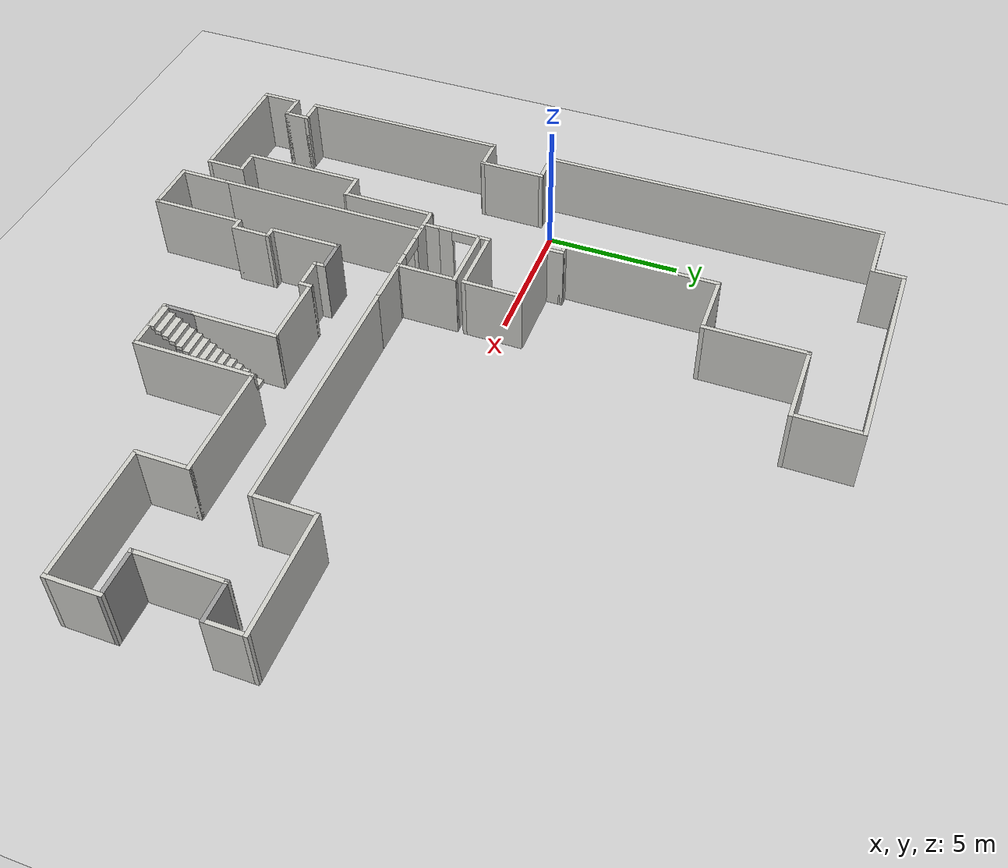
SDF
<sdf version="1.7">
 <world name="default">
  <light name="sun" type="directional">
   <pose>0 0 10 0 -0 0</pose>
   <diffuse>0.8 0.8 0.8 1</diffuse>
   <specular>0.2 0.2 0.2 1</specular>
   <attenuation>
    <range>1000</range>
    <constant>0.9</constant>
    <linear>0.01</linear>
    <quadratic>0.001</quadratic>
   </attenuation>
   <direction>-0.5 0.1 -0.9</direction>
   <spot><inner_angle>0</inner_angle><outer_angle>0</outer_angle><falloff>0</falloff></spot>
  </light>
  <model name="ground_plane">
   <static>1</static>
   <link name="link">
    <collision name="collision">
     <geometry><plane><normal>0 0 1</normal><size>100 100</size></plane></geometry>
     <surface>
      <contact><collide_bitmask>65535</collide_bitmask></contact>
      <friction><ode><mu>100</mu><mu2>50</mu2></ode></friction>
     </surface>
    </collision>
    <visual name="visual">
     <cast_shadows>0</cast_shadows>
     <geometry><plane><normal>0 0 1</normal><size>100 100</size></plane></geometry>
     <material>
      <script><uri>file://media/materials/scripts/gazebo.material</uri><name>Gazebo/Grey</name></script>
     </material>
    </visual>
   </link>
  </model>
  <gravity>0 0 -9.8</gravity>
  <magnetic_field>6e-06 2.3e-05 -4.2e-05</magnetic_field>
  <atmosphere type="adiabatic"/>
  <physics type="ode">
   <max_step_size>0.001</max_step_size>
   <real_time_factor>1</real_time_factor>
   <real_time_update_rate>1000</real_time_update_rate>
  </physics>
  <scene><ambient>0.4 0.4 0.4 1</ambient><background>0.7 0.7 0.7 1</background><shadows>1</shadows></scene>
  <spherical_coordinates>
   <surface_model>EARTH_WGS84</surface_model>
   <latitude_deg>0</latitude_deg>
   <longitude_deg>0</longitude_deg>
   <elevation>0</elevation>
   <heading_deg>0</heading_deg>
  </spherical_coordinates>
  <model name="map_depo">
   <link name="Stairs_0">
    <visual name="Stairs_0_Visual_9">
     <pose>1.22447 -8.88721 1.58333 0 -0 0</pose>
     <geometry><box><size>1 0.233333 0.166667</size></box></geometry>
     <material>
      <script><uri>file://media/materials/scripts/gazebo.material</uri><name>Gazebo/CeilingTiled</name></script>
      <ambient>1 1 1 1</ambient>
      <shader type="pixel"/>
     </material>
     <meta><layer>0</layer></meta>
    </visual>
    <visual name="Stairs_0_Visual_12">
     <pose>1.22447 -9.58721 2.08333 0 -0 0</pose>
     <geometry><box><size>1 0.233333 0.166667</size></box></geometry>
     <material>
      <script><uri>file://media/materials/scripts/gazebo.material</uri><name>Gazebo/CeilingTiled</name></script>
      <ambient>1 1 1 1</ambient>
      <shader type="pixel"/>
     </material>
     <meta><layer>0</layer></meta>
    </visual>
    <visual name="Stairs_0_Visual_4">
     <pose>1.22447 -7.72054 0.75 0 -0 0</pose>
     <geometry><box><size>1 0.233333 0.166667</size></box></geometry>
     <material>
      <script><uri>file://media/materials/scripts/gazebo.material</uri><name>Gazebo/CeilingTiled</name></script>
      <ambient>1 1 1 1</ambient>
      <shader type="pixel"/>
     </material>
     <meta><layer>0</layer></meta>
    </visual>
    <visual name="Stairs_0_Visual_7">
     <pose>1.22447 -8.42054 1.25 0 -0 0</pose>
     <geometry><box><size>1 0.233333 0.166667</size></box></geometry>
     <material>
      <script><uri>file://media/materials/scripts/gazebo.material</uri><name>Gazebo/CeilingTiled</name></script>
      <ambient>1 1 1 1</ambient>
      <shader type="pixel"/>
     </material>
     <meta><layer>0</layer></meta>
    </visual>
    <visual name="Stairs_0_Visual_14">
     <pose>1.22447 -10.0539 2.41667 0 -0 0</pose>
     <geometry><box><size>1 0.233333 0.166667</size></box></geometry>
     <material>
      <script><uri>file://media/materials/scripts/gazebo.material</uri><name>Gazebo/CeilingTiled</name></script>
      <ambient>1 1 1 1</ambient>
      <shader type="pixel"/>
     </material>
     <meta><layer>0</layer></meta>
    </visual>
    <visual name="Stairs_0_Visual_0">
     <pose>1.22447 -6.78721 0.083333 0 -0 0</pose>
     <geometry><box><size>1 0.233333 0.166667</size></box></geometry>
     <material>
      <script><uri>file://media/materials/scripts/gazebo.material</uri><name>Gazebo/CeilingTiled</name></script>
      <ambient>1 1 1 1</ambient>
      <shader type="pixel"/>
     </material>
     <meta><layer>0</layer></meta>
    </visual>
    <visual name="Stairs_0_Visual_10">
     <pose>1.22447 -9.12054 1.75 0 -0 0</pose>
     <geometry><box><size>1 0.233333 0.166667</size></box></geometry>
     <material>
      <script><uri>file://media/materials/scripts/gazebo.material</uri><name>Gazebo/CeilingTiled</name></script>
      <ambient>1 1 1 1</ambient>
      <shader type="pixel"/>
     </material>
     <meta><layer>0</layer></meta>
    </visual>
    <visual name="Stairs_0_Visual_6">
     <pose>1.22447 -8.18721 1.08333 0 -0 0</pose>
     <geometry><box><size>1 0.233333 0.166667</size></box></geometry>
     <material>
      <script><uri>file://media/materials/scripts/gazebo.material</uri><name>Gazebo/CeilingTiled</name></script>
      <ambient>1 1 1 1</ambient>
      <shader type="pixel"/>
     </material>
     <meta><layer>0</layer></meta>
    </visual>
    <visual name="Stairs_0_Visual_5">
     <pose>1.22447 -7.95388 0.916667 0 -0 0</pose>
     <geometry><box><size>1 0.233333 0.166667</size></box></geometry>
     <material>
      <script><uri>file://media/materials/scripts/gazebo.material</uri><name>Gazebo/CeilingTiled</name></script>
      <ambient>1 1 1 1</ambient>
      <shader type="pixel"/>
     </material>
     <meta><layer>0</layer></meta>
    </visual>
    <visual name="Stairs_0_Visual_2">
     <pose>1.22447 -7.25387 0.416667 0 -0 0</pose>
     <geometry><box><size>1 0.233333 0.166667</size></box></geometry>
     <material>
      <script><uri>file://media/materials/scripts/gazebo.material</uri><name>Gazebo/CeilingTiled</name></script>
      <ambient>1 1 1 1</ambient>
      <shader type="pixel"/>
     </material>
     <meta><layer>0</layer></meta>
    </visual>
    <visual name="Stairs_0_Visual_8">
     <pose>1.22447 -8.65388 1.41667 0 -0 0</pose>
     <geometry><box><size>1 0.233333 0.166667</size></box></geometry>
     <material>
      <script><uri>file://media/materials/scripts/gazebo.material</uri><name>Gazebo/CeilingTiled</name></script>
      <ambient>1 1 1 1</ambient>
      <shader type="pixel"/>
     </material>
     <meta><layer>0</layer></meta>
    </visual>
    <visual name="Stairs_0_Visual_13">
     <pose>1.22447 -9.82054 2.25 0 -0 0</pose>
     <geometry><box><size>1 0.233333 0.166667</size></box></geometry>
     <material>
      <script><uri>file://media/materials/scripts/gazebo.material</uri><name>Gazebo/CeilingTiled</name></script>
      <ambient>1 1 1 1</ambient>
      <shader type="pixel"/>
     </material>
     <meta><layer>0</layer></meta>
    </visual>
    <visual name="Stairs_0_Visual_1">
     <pose>1.22447 -7.02054 0.25 0 -0 0</pose>
     <geometry><box><size>1 0.233333 0.166667</size></box></geometry>
     <material>
      <script><uri>file://media/materials/scripts/gazebo.material</uri><name>Gazebo/CeilingTiled</name></script>
      <ambient>1 1 1 1</ambient>
      <shader type="pixel"/>
     </material>
     <meta><layer>0</layer></meta>
    </visual>
    <visual name="Stairs_0_Visual_11">
     <pose>1.22447 -9.35388 1.91667 0 -0 0</pose>
     <geometry><box><size>1 0.233333 0.166667</size></box></geometry>
     <material>
      <script><uri>file://media/materials/scripts/gazebo.material</uri><name>Gazebo/CeilingTiled</name></script>
      <ambient>1 1 1 1</ambient>
      <shader type="pixel"/>
     </material>
     <meta><layer>0</layer></meta>
    </visual>
    <visual name="Stairs_0_Visual_3">
     <pose>1.22447 -7.48721 0.583333 0 -0 0</pose>
     <geometry><box><size>1 0.233333 0.166667</size></box></geometry>
     <material>
      <script><uri>file://media/materials/scripts/gazebo.material</uri><name>Gazebo/CeilingTiled</name></script>
      <ambient>1 1 1 1</ambient>
      <shader type="pixel"/>
     </material>
     <meta><layer>0</layer></meta>
    </visual>
    <collision name="Stairs_0_Collision_11">
     <pose>1.22447 -9.35388 1.91667 0 -0 0</pose>
     <geometry><box><size>1 0.233333 0.166667</size></box></geometry>
     <surface>
      <friction>
       <ode><mu>1</mu><mu2>1</mu2><fdir1>0 0 0</fdir1><slip1>0</slip1><slip2>0</slip2></ode>
       <torsional>
        <coefficient>1</coefficient>
        <patch_radius>0</patch_radius>
        <surface_radius>0</surface_radius>
        <use_patch_radius>1</use_patch_radius>
        <ode><slip>0</slip></ode>
       </torsional>
      </friction>
      <bounce><restitution_coefficient>0</restitution_coefficient><threshold>1e+06</threshold></bounce>
      <contact>
       <collide_without_contact>0</collide_without_contact>
       <collide_without_contact_bitmask>1</collide_without_contact_bitmask>
       <collide_bitmask>1</collide_bitmask>
       <ode>
        <soft_cfm>0</soft_cfm>
        <soft_erp>0.2</soft_erp>
        <kp>1e+13</kp>
        <kd>1</kd>
        <max_vel>0.01</max_vel>
        <min_depth>0</min_depth>
       </ode>
       <bullet>
        <split_impulse>1</split_impulse>
        <split_impulse_penetration_threshold>-0.01</split_impulse_penetration_threshold>
        <soft_cfm>0</soft_cfm>
        <soft_erp>0.2</soft_erp>
        <kp>1e+13</kp>
        <kd>1</kd>
       </bullet>
      </contact>
     </surface>
    </collision>
    <collision name="Stairs_0_Collision_0">
     <pose>1.22447 -6.78721 0.083333 0 -0 0</pose>
     <geometry><box><size>1 0.233333 0.166667</size></box></geometry>
     <surface>
      <friction>
       <ode><mu>1</mu><mu2>1</mu2><fdir1>0 0 0</fdir1><slip1>0</slip1><slip2>0</slip2></ode>
       <torsional>
        <coefficient>1</coefficient>
        <patch_radius>0</patch_radius>
        <surface_radius>0</surface_radius>
        <use_patch_radius>1</use_patch_radius>
        <ode><slip>0</slip></ode>
       </torsional>
      </friction>
      <bounce><restitution_coefficient>0</restitution_coefficient><threshold>1e+06</threshold></bounce>
      <contact>
       <collide_without_contact>0</collide_without_contact>
       <collide_without_contact_bitmask>1</collide_without_contact_bitmask>
       <collide_bitmask>1</collide_bitmask>
       <ode>
        <soft_cfm>0</soft_cfm>
        <soft_erp>0.2</soft_erp>
        <kp>1e+13</kp>
        <kd>1</kd>
        <max_vel>0.01</max_vel>
        <min_depth>0</min_depth>
       </ode>
       <bullet>
        <split_impulse>1</split_impulse>
        <split_impulse_penetration_threshold>-0.01</split_impulse_penetration_threshold>
        <soft_cfm>0</soft_cfm>
        <soft_erp>0.2</soft_erp>
        <kp>1e+13</kp>
        <kd>1</kd>
       </bullet>
      </contact>
     </surface>
    </collision>
    <collision name="Stairs_0_Collision_3">
     <pose>1.22447 -7.48721 0.583333 0 -0 0</pose>
     <geometry><box><size>1 0.233333 0.166667</size></box></geometry>
     <surface>
      <friction>
       <ode><mu>1</mu><mu2>1</mu2><fdir1>0 0 0</fdir1><slip1>0</slip1><slip2>0</slip2></ode>
       <torsional>
        <coefficient>1</coefficient>
        <patch_radius>0</patch_radius>
        <surface_radius>0</surface_radius>
        <use_patch_radius>1</use_patch_radius>
        <ode><slip>0</slip></ode>
       </torsional>
      </friction>
      <bounce><restitution_coefficient>0</restitution_coefficient><threshold>1e+06</threshold></bounce>
      <contact>
       <collide_without_contact>0</collide_without_contact>
       <collide_without_contact_bitmask>1</collide_without_contact_bitmask>
       <collide_bitmask>1</collide_bitmask>
       <ode>
        <soft_cfm>0</soft_cfm>
        <soft_erp>0.2</soft_erp>
        <kp>1e+13</kp>
        <kd>1</kd>
        <max_vel>0.01</max_vel>
        <min_depth>0</min_depth>
       </ode>
       <bullet>
        <split_impulse>1</split_impulse>
        <split_impulse_penetration_threshold>-0.01</split_impulse_penetration_threshold>
        <soft_cfm>0</soft_cfm>
        <soft_erp>0.2</soft_erp>
        <kp>1e+13</kp>
        <kd>1</kd>
       </bullet>
      </contact>
     </surface>
    </collision>
    <collision name="Stairs_0_Collision_9">
     <pose>1.22447 -8.88721 1.58333 0 -0 0</pose>
     <geometry><box><size>1 0.233333 0.166667</size></box></geometry>
     <surface>
      <friction>
       <ode><mu>1</mu><mu2>1</mu2><fdir1>0 0 0</fdir1><slip1>0</slip1><slip2>0</slip2></ode>
       <torsional>
        <coefficient>1</coefficient>
        <patch_radius>0</patch_radius>
        <surface_radius>0</surface_radius>
        <use_patch_radius>1</use_patch_radius>
        <ode><slip>0</slip></ode>
       </torsional>
      </friction>
      <bounce><restitution_coefficient>0</restitution_coefficient><threshold>1e+06</threshold></bounce>
      <contact>
       <collide_without_contact>0</collide_without_contact>
       <collide_without_contact_bitmask>1</collide_without_contact_bitmask>
       <collide_bitmask>1</collide_bitmask>
       <ode>
        <soft_cfm>0</soft_cfm>
        <soft_erp>0.2</soft_erp>
        <kp>1e+13</kp>
        <kd>1</kd>
        <max_vel>0.01</max_vel>
        <min_depth>0</min_depth>
       </ode>
       <bullet>
        <split_impulse>1</split_impulse>
        <split_impulse_penetration_threshold>-0.01</split_impulse_penetration_threshold>
        <soft_cfm>0</soft_cfm>
        <soft_erp>0.2</soft_erp>
        <kp>1e+13</kp>
        <kd>1</kd>
       </bullet>
      </contact>
     </surface>
    </collision>
    <collision name="Stairs_0_Collision_8">
     <pose>1.22447 -8.65388 1.41667 0 -0 0</pose>
     <geometry><box><size>1 0.233333 0.166667</size></box></geometry>
     <surface>
      <friction>
       <ode><mu>1</mu><mu2>1</mu2><fdir1>0 0 0</fdir1><slip1>0</slip1><slip2>0</slip2></ode>
       <torsional>
        <coefficient>1</coefficient>
        <patch_radius>0</patch_radius>
        <surface_radius>0</surface_radius>
        <use_patch_radius>1</use_patch_radius>
        <ode><slip>0</slip></ode>
       </torsional>
      </friction>
      <bounce><restitution_coefficient>0</restitution_coefficient><threshold>1e+06</threshold></bounce>
      <contact>
       <collide_without_contact>0</collide_without_contact>
       <collide_without_contact_bitmask>1</collide_without_contact_bitmask>
       <collide_bitmask>1</collide_bitmask>
       <ode>
        <soft_cfm>0</soft_cfm>
        <soft_erp>0.2</soft_erp>
        <kp>1e+13</kp>
        <kd>1</kd>
        <max_vel>0.01</max_vel>
        <min_depth>0</min_depth>
       </ode>
       <bullet>
        <split_impulse>1</split_impulse>
        <split_impulse_penetration_threshold>-0.01</split_impulse_penetration_threshold>
        <soft_cfm>0</soft_cfm>
        <soft_erp>0.2</soft_erp>
        <kp>1e+13</kp>
        <kd>1</kd>
       </bullet>
      </contact>
     </surface>
    </collision>
    <collision name="Stairs_0_Collision_6">
     <pose>1.22447 -8.18721 1.08333 0 -0 0</pose>
     <geometry><box><size>1 0.233333 0.166667</size></box></geometry>
     <surface>
      <friction>
       <ode><mu>1</mu><mu2>1</mu2><fdir1>0 0 0</fdir1><slip1>0</slip1><slip2>0</slip2></ode>
       <torsional>
        <coefficient>1</coefficient>
        <patch_radius>0</patch_radius>
        <surface_radius>0</surface_radius>
        <use_patch_radius>1</use_patch_radius>
        <ode><slip>0</slip></ode>
       </torsional>
      </friction>
      <bounce><restitution_coefficient>0</restitution_coefficient><threshold>1e+06</threshold></bounce>
      <contact>
       <collide_without_contact>0</collide_without_contact>
       <collide_without_contact_bitmask>1</collide_without_contact_bitmask>
       <collide_bitmask>1</collide_bitmask>
       <ode>
        <soft_cfm>0</soft_cfm>
        <soft_erp>0.2</soft_erp>
        <kp>1e+13</kp>
        <kd>1</kd>
        <max_vel>0.01</max_vel>
        <min_depth>0</min_depth>
       </ode>
       <bullet>
        <split_impulse>1</split_impulse>
        <split_impulse_penetration_threshold>-0.01</split_impulse_penetration_threshold>
        <soft_cfm>0</soft_cfm>
        <soft_erp>0.2</soft_erp>
        <kp>1e+13</kp>
        <kd>1</kd>
       </bullet>
      </contact>
     </surface>
    </collision>
    <collision name="Stairs_0_Collision_13">
     <pose>1.22447 -9.82054 2.25 0 -0 0</pose>
     <geometry><box><size>1 0.233333 0.166667</size></box></geometry>
     <surface>
      <friction>
       <ode><mu>1</mu><mu2>1</mu2><fdir1>0 0 0</fdir1><slip1>0</slip1><slip2>0</slip2></ode>
       <torsional>
        <coefficient>1</coefficient>
        <patch_radius>0</patch_radius>
        <surface_radius>0</surface_radius>
        <use_patch_radius>1</use_patch_radius>
        <ode><slip>0</slip></ode>
       </torsional>
      </friction>
      <bounce><restitution_coefficient>0</restitution_coefficient><threshold>1e+06</threshold></bounce>
      <contact>
       <collide_without_contact>0</collide_without_contact>
       <collide_without_contact_bitmask>1</collide_without_contact_bitmask>
       <collide_bitmask>1</collide_bitmask>
       <ode>
        <soft_cfm>0</soft_cfm>
        <soft_erp>0.2</soft_erp>
        <kp>1e+13</kp>
        <kd>1</kd>
        <max_vel>0.01</max_vel>
        <min_depth>0</min_depth>
       </ode>
       <bullet>
        <split_impulse>1</split_impulse>
        <split_impulse_penetration_threshold>-0.01</split_impulse_penetration_threshold>
        <soft_cfm>0</soft_cfm>
        <soft_erp>0.2</soft_erp>
        <kp>1e+13</kp>
        <kd>1</kd>
       </bullet>
      </contact>
     </surface>
    </collision>
    <collision name="Stairs_0_Collision_12">
     <pose>1.22447 -9.58721 2.08333 0 -0 0</pose>
     <geometry><box><size>1 0.233333 0.166667</size></box></geometry>
     <surface>
      <friction>
       <ode><mu>1</mu><mu2>1</mu2><fdir1>0 0 0</fdir1><slip1>0</slip1><slip2>0</slip2></ode>
       <torsional>
        <coefficient>1</coefficient>
        <patch_radius>0</patch_radius>
        <surface_radius>0</surface_radius>
        <use_patch_radius>1</use_patch_radius>
        <ode><slip>0</slip></ode>
       </torsional>
      </friction>
      <bounce><restitution_coefficient>0</restitution_coefficient><threshold>1e+06</threshold></bounce>
      <contact>
       <collide_without_contact>0</collide_without_contact>
       <collide_without_contact_bitmask>1</collide_without_contact_bitmask>
       <collide_bitmask>1</collide_bitmask>
       <ode>
        <soft_cfm>0</soft_cfm>
        <soft_erp>0.2</soft_erp>
        <kp>1e+13</kp>
        <kd>1</kd>
        <max_vel>0.01</max_vel>
        <min_depth>0</min_depth>
       </ode>
       <bullet>
        <split_impulse>1</split_impulse>
        <split_impulse_penetration_threshold>-0.01</split_impulse_penetration_threshold>
        <soft_cfm>0</soft_cfm>
        <soft_erp>0.2</soft_erp>
        <kp>1e+13</kp>
        <kd>1</kd>
       </bullet>
      </contact>
     </surface>
    </collision>
    <collision name="Stairs_0_Collision_4">
     <pose>1.22447 -7.72054 0.75 0 -0 0</pose>
     <geometry><box><size>1 0.233333 0.166667</size></box></geometry>
     <surface>
      <friction>
       <ode><mu>1</mu><mu2>1</mu2><fdir1>0 0 0</fdir1><slip1>0</slip1><slip2>0</slip2></ode>
       <torsional>
        <coefficient>1</coefficient>
        <patch_radius>0</patch_radius>
        <surface_radius>0</surface_radius>
        <use_patch_radius>1</use_patch_radius>
        <ode><slip>0</slip></ode>
       </torsional>
      </friction>
      <bounce><restitution_coefficient>0</restitution_coefficient><threshold>1e+06</threshold></bounce>
      <contact>
       <collide_without_contact>0</collide_without_contact>
       <collide_without_contact_bitmask>1</collide_without_contact_bitmask>
       <collide_bitmask>1</collide_bitmask>
       <ode>
        <soft_cfm>0</soft_cfm>
        <soft_erp>0.2</soft_erp>
        <kp>1e+13</kp>
        <kd>1</kd>
        <max_vel>0.01</max_vel>
        <min_depth>0</min_depth>
       </ode>
       <bullet>
        <split_impulse>1</split_impulse>
        <split_impulse_penetration_threshold>-0.01</split_impulse_penetration_threshold>
        <soft_cfm>0</soft_cfm>
        <soft_erp>0.2</soft_erp>
        <kp>1e+13</kp>
        <kd>1</kd>
       </bullet>
      </contact>
     </surface>
    </collision>
    <collision name="Stairs_0_Collision_7">
     <pose>1.22447 -8.42054 1.25 0 -0 0</pose>
     <geometry><box><size>1 0.233333 0.166667</size></box></geometry>
     <surface>
      <friction>
       <ode><mu>1</mu><mu2>1</mu2><fdir1>0 0 0</fdir1><slip1>0</slip1><slip2>0</slip2></ode>
       <torsional>
        <coefficient>1</coefficient>
        <patch_radius>0</patch_radius>
        <surface_radius>0</surface_radius>
        <use_patch_radius>1</use_patch_radius>
        <ode><slip>0</slip></ode>
       </torsional>
      </friction>
      <bounce><restitution_coefficient>0</restitution_coefficient><threshold>1e+06</threshold></bounce>
      <contact>
       <collide_without_contact>0</collide_without_contact>
       <collide_without_contact_bitmask>1</collide_without_contact_bitmask>
       <collide_bitmask>1</collide_bitmask>
       <ode>
        <soft_cfm>0</soft_cfm>
        <soft_erp>0.2</soft_erp>
        <kp>1e+13</kp>
        <kd>1</kd>
        <max_vel>0.01</max_vel>
        <min_depth>0</min_depth>
       </ode>
       <bullet>
        <split_impulse>1</split_impulse>
        <split_impulse_penetration_threshold>-0.01</split_impulse_penetration_threshold>
        <soft_cfm>0</soft_cfm>
        <soft_erp>0.2</soft_erp>
        <kp>1e+13</kp>
        <kd>1</kd>
       </bullet>
      </contact>
     </surface>
    </collision>
    <collision name="Stairs_0_Collision_5">
     <pose>1.22447 -7.95388 0.916667 0 -0 0</pose>
     <geometry><box><size>1 0.233333 0.166667</size></box></geometry>
     <surface>
      <friction>
       <ode><mu>1</mu><mu2>1</mu2><fdir1>0 0 0</fdir1><slip1>0</slip1><slip2>0</slip2></ode>
       <torsional>
        <coefficient>1</coefficient>
        <patch_radius>0</patch_radius>
        <surface_radius>0</surface_radius>
        <use_patch_radius>1</use_patch_radius>
        <ode><slip>0</slip></ode>
       </torsional>
      </friction>
      <bounce><restitution_coefficient>0</restitution_coefficient><threshold>1e+06</threshold></bounce>
      <contact>
       <collide_without_contact>0</collide_without_contact>
       <collide_without_contact_bitmask>1</collide_without_contact_bitmask>
       <collide_bitmask>1</collide_bitmask>
       <ode>
        <soft_cfm>0</soft_cfm>
        <soft_erp>0.2</soft_erp>
        <kp>1e+13</kp>
        <kd>1</kd>
        <max_vel>0.01</max_vel>
        <min_depth>0</min_depth>
       </ode>
       <bullet>
        <split_impulse>1</split_impulse>
        <split_impulse_penetration_threshold>-0.01</split_impulse_penetration_threshold>
        <soft_cfm>0</soft_cfm>
        <soft_erp>0.2</soft_erp>
        <kp>1e+13</kp>
        <kd>1</kd>
       </bullet>
      </contact>
     </surface>
    </collision>
    <collision name="Stairs_0_Collision_10">
     <pose>1.22447 -9.12054 1.75 0 -0 0</pose>
     <geometry><box><size>1 0.233333 0.166667</size></box></geometry>
     <surface>
      <friction>
       <ode><mu>1</mu><mu2>1</mu2><fdir1>0 0 0</fdir1><slip1>0</slip1><slip2>0</slip2></ode>
       <torsional>
        <coefficient>1</coefficient>
        <patch_radius>0</patch_radius>
        <surface_radius>0</surface_radius>
        <use_patch_radius>1</use_patch_radius>
        <ode><slip>0</slip></ode>
       </torsional>
      </friction>
      <bounce><restitution_coefficient>0</restitution_coefficient><threshold>1e+06</threshold></bounce>
      <contact>
       <collide_without_contact>0</collide_without_contact>
       <collide_without_contact_bitmask>1</collide_without_contact_bitmask>
       <collide_bitmask>1</collide_bitmask>
       <ode>
        <soft_cfm>0</soft_cfm>
        <soft_erp>0.2</soft_erp>
        <kp>1e+13</kp>
        <kd>1</kd>
        <max_vel>0.01</max_vel>
        <min_depth>0</min_depth>
       </ode>
       <bullet>
        <split_impulse>1</split_impulse>
        <split_impulse_penetration_threshold>-0.01</split_impulse_penetration_threshold>
        <soft_cfm>0</soft_cfm>
        <soft_erp>0.2</soft_erp>
        <kp>1e+13</kp>
        <kd>1</kd>
       </bullet>
      </contact>
     </surface>
    </collision>
    <collision name="Stairs_0_Collision_2">
     <pose>1.22447 -7.25387 0.416667 0 -0 0</pose>
     <geometry><box><size>1 0.233333 0.166667</size></box></geometry>
     <surface>
      <friction>
       <ode><mu>1</mu><mu2>1</mu2><fdir1>0 0 0</fdir1><slip1>0</slip1><slip2>0</slip2></ode>
       <torsional>
        <coefficient>1</coefficient>
        <patch_radius>0</patch_radius>
        <surface_radius>0</surface_radius>
        <use_patch_radius>1</use_patch_radius>
        <ode><slip>0</slip></ode>
       </torsional>
      </friction>
      <bounce><restitution_coefficient>0</restitution_coefficient><threshold>1e+06</threshold></bounce>
      <contact>
       <collide_without_contact>0</collide_without_contact>
       <collide_without_contact_bitmask>1</collide_without_contact_bitmask>
       <collide_bitmask>1</collide_bitmask>
       <ode>
        <soft_cfm>0</soft_cfm>
        <soft_erp>0.2</soft_erp>
        <kp>1e+13</kp>
        <kd>1</kd>
        <max_vel>0.01</max_vel>
        <min_depth>0</min_depth>
       </ode>
       <bullet>
        <split_impulse>1</split_impulse>
        <split_impulse_penetration_threshold>-0.01</split_impulse_penetration_threshold>
        <soft_cfm>0</soft_cfm>
        <soft_erp>0.2</soft_erp>
        <kp>1e+13</kp>
        <kd>1</kd>
       </bullet>
      </contact>
     </surface>
    </collision>
    <collision name="Stairs_0_Collision_14">
     <pose>1.22447 -10.0539 2.41667 0 -0 0</pose>
     <geometry><box><size>1 0.233333 0.166667</size></box></geometry>
     <surface>
      <friction>
       <ode><mu>1</mu><mu2>1</mu2><fdir1>0 0 0</fdir1><slip1>0</slip1><slip2>0</slip2></ode>
       <torsional>
        <coefficient>1</coefficient>
        <patch_radius>0</patch_radius>
        <surface_radius>0</surface_radius>
        <use_patch_radius>1</use_patch_radius>
        <ode><slip>0</slip></ode>
       </torsional>
      </friction>
      <bounce><restitution_coefficient>0</restitution_coefficient><threshold>1e+06</threshold></bounce>
      <contact>
       <collide_without_contact>0</collide_without_contact>
       <collide_without_contact_bitmask>1</collide_without_contact_bitmask>
       <collide_bitmask>1</collide_bitmask>
       <ode>
        <soft_cfm>0</soft_cfm>
        <soft_erp>0.2</soft_erp>
        <kp>1e+13</kp>
        <kd>1</kd>
        <max_vel>0.01</max_vel>
        <min_depth>0</min_depth>
       </ode>
       <bullet>
        <split_impulse>1</split_impulse>
        <split_impulse_penetration_threshold>-0.01</split_impulse_penetration_threshold>
        <soft_cfm>0</soft_cfm>
        <soft_erp>0.2</soft_erp>
        <kp>1e+13</kp>
        <kd>1</kd>
       </bullet>
      </contact>
     </surface>
    </collision>
    <collision name="Stairs_0_Collision_1">
     <pose>1.22447 -7.02054 0.25 0 -0 0</pose>
     <geometry><box><size>1 0.233333 0.166667</size></box></geometry>
     <surface>
      <friction>
       <ode><mu>1</mu><mu2>1</mu2><fdir1>0 0 0</fdir1><slip1>0</slip1><slip2>0</slip2></ode>
       <torsional>
        <coefficient>1</coefficient>
        <patch_radius>0</patch_radius>
        <surface_radius>0</surface_radius>
        <use_patch_radius>1</use_patch_radius>
        <ode><slip>0</slip></ode>
       </torsional>
      </friction>
      <bounce><restitution_coefficient>0</restitution_coefficient><threshold>1e+06</threshold></bounce>
      <contact>
       <collide_without_contact>0</collide_without_contact>
       <collide_without_contact_bitmask>1</collide_without_contact_bitmask>
       <collide_bitmask>1</collide_bitmask>
       <ode>
        <soft_cfm>0</soft_cfm>
        <soft_erp>0.2</soft_erp>
        <kp>1e+13</kp>
        <kd>1</kd>
        <max_vel>0.01</max_vel>
        <min_depth>0</min_depth>
       </ode>
       <bullet>
        <split_impulse>1</split_impulse>
        <split_impulse_penetration_threshold>-0.01</split_impulse_penetration_threshold>
        <soft_cfm>0</soft_cfm>
        <soft_erp>0.2</soft_erp>
        <kp>1e+13</kp>
        <kd>1</kd>
       </bullet>
      </contact>
     </surface>
    </collision>
   </link>
   <link name="Wall_102">
    <pose>-3.05165 -3.52199 0 0 -0 3.14071</pose>
    <inertial>
     <mass>1</mass>
     <inertia><ixx>1</ixx><ixy>0</ixy><ixz>0</ixz><iyy>1</iyy><iyz>0</iyz><izz>1</izz></inertia>
    </inertial>
    <visual name="Wall_102_Visual">
     <pose>0 0 1.25 0 -0 0</pose>
     <geometry><box><size>1.87377 0.15 2.5</size></box></geometry>
     <material>
      <script><uri>file://media/materials/scripts/gazebo.material</uri><name>Gazebo/CeilingTiled</name></script>
      <ambient>1 1 1 1</ambient>
      <shader type="pixel"><normal_map>__default__</normal_map></shader>
      <diffuse>1 1 1 1</diffuse>
      <specular>0 0 0 1</specular>
      <emissive>0 0 0 1</emissive>
     </material>
     <meta><layer>0</layer></meta>
    </visual>
    <collision name="Wall_102_Collision">
     <pose>0 0 1.25 0 -0 0</pose>
     <geometry><box><size>1.87377 0.15 2.5</size></box></geometry>
     <surface>
      <friction>
       <ode><mu>1</mu><mu2>1</mu2><fdir1>0 0 0</fdir1><slip1>0</slip1><slip2>0</slip2></ode>
       <torsional>
        <coefficient>1</coefficient>
        <patch_radius>0</patch_radius>
        <surface_radius>0</surface_radius>
        <use_patch_radius>1</use_patch_radius>
        <ode><slip>0</slip></ode>
       </torsional>
      </friction>
      <bounce><restitution_coefficient>0</restitution_coefficient><threshold>1e+06</threshold></bounce>
      <contact>
       <collide_without_contact>0</collide_without_contact>
       <collide_without_contact_bitmask>1</collide_without_contact_bitmask>
       <collide_bitmask>1</collide_bitmask>
       <ode>
        <soft_cfm>0</soft_cfm>
        <soft_erp>0.2</soft_erp>
        <kp>1e+13</kp>
        <kd>1</kd>
        <max_vel>0.01</max_vel>
        <min_depth>0</min_depth>
       </ode>
       <bullet>
        <split_impulse>1</split_impulse>
        <split_impulse_penetration_threshold>-0.01</split_impulse_penetration_threshold>
        <soft_cfm>0</soft_cfm>
        <soft_erp>0.2</soft_erp>
        <kp>1e+13</kp>
        <kd>1</kd>
       </bullet>
      </contact>
     </surface>
    </collision>
   </link>
   <link name="Wall_11">
    <pose>-9.3996 12.685 0 0 -0 1.5708</pose>
    <visual name="Wall_11_Visual">
     <pose>0 0 1.25 0 -0 0</pose>
     <geometry><box><size>1.25 0.15 2.5</size></box></geometry>
     <material>
      <script><uri>file://media/materials/scripts/gazebo.material</uri><name>Gazebo/CeilingTiled</name></script>
      <ambient>1 1 1 1</ambient>
      <shader type="pixel"/>
     </material>
     <meta><layer>0</layer></meta>
    </visual>
    <collision name="Wall_11_Collision">
     <pose>0 0 1.25 0 -0 0</pose>
     <geometry><box><size>1.25 0.15 2.5</size></box></geometry>
     <surface>
      <friction>
       <ode><mu>1</mu><mu2>1</mu2><fdir1>0 0 0</fdir1><slip1>0</slip1><slip2>0</slip2></ode>
       <torsional>
        <coefficient>1</coefficient>
        <patch_radius>0</patch_radius>
        <surface_radius>0</surface_radius>
        <use_patch_radius>1</use_patch_radius>
        <ode><slip>0</slip></ode>
       </torsional>
      </friction>
      <bounce><restitution_coefficient>0</restitution_coefficient><threshold>1e+06</threshold></bounce>
      <contact>
       <collide_without_contact>0</collide_without_contact>
       <collide_without_contact_bitmask>1</collide_without_contact_bitmask>
       <collide_bitmask>1</collide_bitmask>
       <ode>
        <soft_cfm>0</soft_cfm>
        <soft_erp>0.2</soft_erp>
        <kp>1e+13</kp>
        <kd>1</kd>
        <max_vel>0.01</max_vel>
        <min_depth>0</min_depth>
       </ode>
       <bullet>
        <split_impulse>1</split_impulse>
        <split_impulse_penetration_threshold>-0.01</split_impulse_penetration_threshold>
        <soft_cfm>0</soft_cfm>
        <soft_erp>0.2</soft_erp>
        <kp>1e+13</kp>
        <kd>1</kd>
       </bullet>
      </contact>
     </surface>
    </collision>
   </link>
   <link name="Wall_12">
    <pose>-5.5996 13.235 0 0 -0 0</pose>
    <visual name="Wall_12_Visual">
     <pose>0 0 1.25 0 -0 0</pose>
     <geometry><box><size>7.75 0.15 2.5</size></box></geometry>
     <material>
      <script><uri>file://media/materials/scripts/gazebo.material</uri><name>Gazebo/CeilingTiled</name></script>
      <ambient>1 1 1 1</ambient>
      <shader type="pixel"/>
     </material>
     <meta><layer>0</layer></meta>
    </visual>
    <collision name="Wall_12_Collision">
     <pose>0 0 1.25 0 -0 0</pose>
     <geometry><box><size>7.75 0.15 2.5</size></box></geometry>
     <surface>
      <friction>
       <ode><mu>1</mu><mu2>1</mu2><fdir1>0 0 0</fdir1><slip1>0</slip1><slip2>0</slip2></ode>
       <torsional>
        <coefficient>1</coefficient>
        <patch_radius>0</patch_radius>
        <surface_radius>0</surface_radius>
        <use_patch_radius>1</use_patch_radius>
        <ode><slip>0</slip></ode>
       </torsional>
      </friction>
      <bounce><restitution_coefficient>0</restitution_coefficient><threshold>1e+06</threshold></bounce>
      <contact>
       <collide_without_contact>0</collide_without_contact>
       <collide_without_contact_bitmask>1</collide_without_contact_bitmask>
       <collide_bitmask>1</collide_bitmask>
       <ode>
        <soft_cfm>0</soft_cfm>
        <soft_erp>0.2</soft_erp>
        <kp>1e+13</kp>
        <kd>1</kd>
        <max_vel>0.01</max_vel>
        <min_depth>0</min_depth>
       </ode>
       <bullet>
        <split_impulse>1</split_impulse>
        <split_impulse_penetration_threshold>-0.01</split_impulse_penetration_threshold>
        <soft_cfm>0</soft_cfm>
        <soft_erp>0.2</soft_erp>
        <kp>1e+13</kp>
        <kd>1</kd>
       </bullet>
      </contact>
     </surface>
    </collision>
   </link>
   <link name="Wall_13">
    <pose>-1.7996 12.06 0 0 0 -1.5708</pose>
    <visual name="Wall_13_Visual">
     <pose>0 0 1.25 0 -0 0</pose>
     <geometry><box><size>2.5 0.15 2.5</size></box></geometry>
     <material>
      <script><uri>file://media/materials/scripts/gazebo.material</uri><name>Gazebo/CeilingTiled</name></script>
      <ambient>1 1 1 1</ambient>
      <shader type="pixel"/>
     </material>
     <meta><layer>0</layer></meta>
    </visual>
    <collision name="Wall_13_Collision">
     <pose>0 0 1.25 0 -0 0</pose>
     <geometry><box><size>2.5 0.15 2.5</size></box></geometry>
     <surface>
      <friction>
       <ode><mu>1</mu><mu2>1</mu2><fdir1>0 0 0</fdir1><slip1>0</slip1><slip2>0</slip2></ode>
       <torsional>
        <coefficient>1</coefficient>
        <patch_radius>0</patch_radius>
        <surface_radius>0</surface_radius>
        <use_patch_radius>1</use_patch_radius>
        <ode><slip>0</slip></ode>
       </torsional>
      </friction>
      <bounce><restitution_coefficient>0</restitution_coefficient><threshold>1e+06</threshold></bounce>
      <contact>
       <collide_without_contact>0</collide_without_contact>
       <collide_without_contact_bitmask>1</collide_without_contact_bitmask>
       <collide_bitmask>1</collide_bitmask>
       <ode>
        <soft_cfm>0</soft_cfm>
        <soft_erp>0.2</soft_erp>
        <kp>1e+13</kp>
        <kd>1</kd>
        <max_vel>0.01</max_vel>
        <min_depth>0</min_depth>
       </ode>
       <bullet>
        <split_impulse>1</split_impulse>
        <split_impulse_penetration_threshold>-0.01</split_impulse_penetration_threshold>
        <soft_cfm>0</soft_cfm>
        <soft_erp>0.2</soft_erp>
        <kp>1e+13</kp>
        <kd>1</kd>
       </bullet>
      </contact>
     </surface>
    </collision>
   </link>
   <link name="Wall_14">
    <pose>-3.21429 10.885 0 0 -0 3.14159</pose>
    <visual name="Wall_14_Visual">
     <pose>0 0 1.25 0 -0 0</pose>
     <geometry><box><size>3 0.15 2.5</size></box></geometry>
     <material>
      <script><uri>file://media/materials/scripts/gazebo.material</uri><name>Gazebo/CeilingTiled</name></script>
      <ambient>1 1 1 1</ambient>
      <shader type="pixel"/>
     </material>
     <meta><layer>0</layer></meta>
    </visual>
    <collision name="Wall_14_Collision">
     <pose>0 0 1.25 0 -0 0</pose>
     <geometry><box><size>3 0.15 2.5</size></box></geometry>
     <surface>
      <friction>
       <ode><mu>1</mu><mu2>1</mu2><fdir1>0 0 0</fdir1><slip1>0</slip1><slip2>0</slip2></ode>
       <torsional>
        <coefficient>1</coefficient>
        <patch_radius>0</patch_radius>
        <surface_radius>0</surface_radius>
        <use_patch_radius>1</use_patch_radius>
        <ode><slip>0</slip></ode>
       </torsional>
      </friction>
      <bounce><restitution_coefficient>0</restitution_coefficient><threshold>1e+06</threshold></bounce>
      <contact>
       <collide_without_contact>0</collide_without_contact>
       <collide_without_contact_bitmask>1</collide_without_contact_bitmask>
       <collide_bitmask>1</collide_bitmask>
       <ode>
        <soft_cfm>0</soft_cfm>
        <soft_erp>0.2</soft_erp>
        <kp>1e+13</kp>
        <kd>1</kd>
        <max_vel>0.01</max_vel>
        <min_depth>0</min_depth>
       </ode>
       <bullet>
        <split_impulse>1</split_impulse>
        <split_impulse_penetration_threshold>-0.01</split_impulse_penetration_threshold>
        <soft_cfm>0</soft_cfm>
        <soft_erp>0.2</soft_erp>
        <kp>1e+13</kp>
        <kd>1</kd>
       </bullet>
      </contact>
     </surface>
    </collision>
   </link>
   <link name="Wall_16">
    <pose>-4.6414 9.08497 0 0 0 -1.5708</pose>
    <visual name="Wall_16_Visual">
     <pose>0 0 1.25 0 -0 0</pose>
     <geometry><box><size>3.75 0.15 2.5</size></box></geometry>
     <material>
      <script><uri>file://media/materials/scripts/gazebo.material</uri><name>Gazebo/CeilingTiled</name></script>
      <ambient>1 1 1 1</ambient>
      <shader type="pixel"/>
     </material>
     <meta><layer>0</layer></meta>
    </visual>
    <collision name="Wall_16_Collision">
     <pose>0 0 1.25 0 -0 0</pose>
     <geometry><box><size>3.75 0.15 2.5</size></box></geometry>
     <surface>
      <friction>
       <ode><mu>1</mu><mu2>1</mu2><fdir1>0 0 0</fdir1><slip1>0</slip1><slip2>0</slip2></ode>
       <torsional>
        <coefficient>1</coefficient>
        <patch_radius>0</patch_radius>
        <surface_radius>0</surface_radius>
        <use_patch_radius>1</use_patch_radius>
        <ode><slip>0</slip></ode>
       </torsional>
      </friction>
      <bounce><restitution_coefficient>0</restitution_coefficient><threshold>1e+06</threshold></bounce>
      <contact>
       <collide_without_contact>0</collide_without_contact>
       <collide_without_contact_bitmask>1</collide_without_contact_bitmask>
       <collide_bitmask>1</collide_bitmask>
       <ode>
        <soft_cfm>0</soft_cfm>
        <soft_erp>0.2</soft_erp>
        <kp>1e+13</kp>
        <kd>1</kd>
        <max_vel>0.01</max_vel>
        <min_depth>0</min_depth>
       </ode>
       <bullet>
        <split_impulse>1</split_impulse>
        <split_impulse_penetration_threshold>-0.01</split_impulse_penetration_threshold>
        <soft_cfm>0</soft_cfm>
        <soft_erp>0.2</soft_erp>
        <kp>1e+13</kp>
        <kd>1</kd>
       </bullet>
      </contact>
     </surface>
    </collision>
   </link>
   <link name="Wall_17">
    <pose>-5.75463 7.27506 0 0 0 -3.13263</pose>
    <visual name="Wall_17_Visual">
     <pose>0 0 1.25 0 -0 0</pose>
     <geometry><box><size>2.39372 0.15 2.5</size></box></geometry>
     <material>
      <script><uri>file://media/materials/scripts/gazebo.material</uri><name>Gazebo/CeilingTiled</name></script>
      <ambient>1 1 1 1</ambient>
      <shader type="pixel"/>
     </material>
     <meta><layer>0</layer></meta>
    </visual>
    <collision name="Wall_17_Collision">
     <pose>0 0 1.25 0 -0 0</pose>
     <geometry><box><size>2.39372 0.15 2.5</size></box></geometry>
     <surface>
      <friction>
       <ode><mu>1</mu><mu2>1</mu2><fdir1>0 0 0</fdir1><slip1>0</slip1><slip2>0</slip2></ode>
       <torsional>
        <coefficient>1</coefficient>
        <patch_radius>0</patch_radius>
        <surface_radius>0</surface_radius>
        <use_patch_radius>1</use_patch_radius>
        <ode><slip>0</slip></ode>
       </torsional>
      </friction>
      <bounce><restitution_coefficient>0</restitution_coefficient><threshold>1e+06</threshold></bounce>
      <contact>
       <collide_without_contact>0</collide_without_contact>
       <collide_without_contact_bitmask>1</collide_without_contact_bitmask>
       <collide_bitmask>1</collide_bitmask>
       <ode>
        <soft_cfm>0</soft_cfm>
        <soft_erp>0.2</soft_erp>
        <kp>1e+13</kp>
        <kd>1</kd>
        <max_vel>0.01</max_vel>
        <min_depth>0</min_depth>
       </ode>
       <bullet>
        <split_impulse>1</split_impulse>
        <split_impulse_penetration_threshold>-0.01</split_impulse_penetration_threshold>
        <soft_cfm>0</soft_cfm>
        <soft_erp>0.2</soft_erp>
        <kp>1e+13</kp>
        <kd>1</kd>
       </bullet>
      </contact>
     </surface>
    </collision>
   </link>
   <link name="Wall_18">
    <pose>-6.87312 4.46486 0 0 0 -1.5708</pose>
    <visual name="Wall_18_Visual">
     <pose>0 0 1.25 0 -0 0</pose>
     <geometry><box><size>5.75 0.15 2.5</size></box></geometry>
     <material>
      <script><uri>file://media/materials/scripts/gazebo.material</uri><name>Gazebo/CeilingTiled</name></script>
      <ambient>1 1 1 1</ambient>
      <shader type="pixel"/>
     </material>
     <meta><layer>0</layer></meta>
    </visual>
    <collision name="Wall_18_Collision">
     <pose>0 0 1.25 0 -0 0</pose>
     <geometry><box><size>5.75 0.15 2.5</size></box></geometry>
     <surface>
      <friction>
       <ode><mu>1</mu><mu2>1</mu2><fdir1>0 0 0</fdir1><slip1>0</slip1><slip2>0</slip2></ode>
       <torsional>
        <coefficient>1</coefficient>
        <patch_radius>0</patch_radius>
        <surface_radius>0</surface_radius>
        <use_patch_radius>1</use_patch_radius>
        <ode><slip>0</slip></ode>
       </torsional>
      </friction>
      <bounce><restitution_coefficient>0</restitution_coefficient><threshold>1e+06</threshold></bounce>
      <contact>
       <collide_without_contact>0</collide_without_contact>
       <collide_without_contact_bitmask>1</collide_without_contact_bitmask>
       <collide_bitmask>1</collide_bitmask>
       <ode>
        <soft_cfm>0</soft_cfm>
        <soft_erp>0.2</soft_erp>
        <kp>1e+13</kp>
        <kd>1</kd>
        <max_vel>0.01</max_vel>
        <min_depth>0</min_depth>
       </ode>
       <bullet>
        <split_impulse>1</split_impulse>
        <split_impulse_penetration_threshold>-0.01</split_impulse_penetration_threshold>
        <soft_cfm>0</soft_cfm>
        <soft_erp>0.2</soft_erp>
        <kp>1e+13</kp>
        <kd>1</kd>
       </bullet>
      </contact>
     </surface>
    </collision>
   </link>
   <link name="Wall_20">
    <pose>-6.69812 1.66486 0 0 -0 0</pose>
    <visual name="Wall_20_Visual">
     <pose>0 0 1.25 0 -0 0</pose>
     <geometry><box><size>0.5 0.15 2.5</size></box></geometry>
     <material>
      <script><uri>file://media/materials/scripts/gazebo.material</uri><name>Gazebo/CeilingTiled</name></script>
      <ambient>1 1 1 1</ambient>
      <shader type="pixel"/>
     </material>
     <meta><layer>0</layer></meta>
    </visual>
    <collision name="Wall_20_Collision">
     <pose>0 0 1.25 0 -0 0</pose>
     <geometry><box><size>0.5 0.15 2.5</size></box></geometry>
     <surface>
      <friction>
       <ode><mu>1</mu><mu2>1</mu2><fdir1>0 0 0</fdir1><slip1>0</slip1><slip2>0</slip2></ode>
       <torsional>
        <coefficient>1</coefficient>
        <patch_radius>0</patch_radius>
        <surface_radius>0</surface_radius>
        <use_patch_radius>1</use_patch_radius>
        <ode><slip>0</slip></ode>
       </torsional>
      </friction>
      <bounce><restitution_coefficient>0</restitution_coefficient><threshold>1e+06</threshold></bounce>
      <contact>
       <collide_without_contact>0</collide_without_contact>
       <collide_without_contact_bitmask>1</collide_without_contact_bitmask>
       <collide_bitmask>1</collide_bitmask>
       <ode>
        <soft_cfm>0</soft_cfm>
        <soft_erp>0.2</soft_erp>
        <kp>1e+13</kp>
        <kd>1</kd>
        <max_vel>0.01</max_vel>
        <min_depth>0</min_depth>
       </ode>
       <bullet>
        <split_impulse>1</split_impulse>
        <split_impulse_penetration_threshold>-0.01</split_impulse_penetration_threshold>
        <soft_cfm>0</soft_cfm>
        <soft_erp>0.2</soft_erp>
        <kp>1e+13</kp>
        <kd>1</kd>
       </bullet>
      </contact>
     </surface>
    </collision>
   </link>
   <link name="Wall_21">
    <pose>-6.52312 1.36486 0 0 0 -1.5708</pose>
    <visual name="Wall_21_Visual">
     <pose>0 0 1.25 0 -0 0</pose>
     <geometry><box><size>0.75 0.15 2.5</size></box></geometry>
     <material>
      <script><uri>file://media/materials/scripts/gazebo.material</uri><name>Gazebo/CeilingTiled</name></script>
      <ambient>1 1 1 1</ambient>
      <shader type="pixel"/>
     </material>
     <meta><layer>0</layer></meta>
    </visual>
    <collision name="Wall_21_Collision">
     <pose>0 0 1.25 0 -0 0</pose>
     <geometry><box><size>0.75 0.15 2.5</size></box></geometry>
     <surface>
      <friction>
       <ode><mu>1</mu><mu2>1</mu2><fdir1>0 0 0</fdir1><slip1>0</slip1><slip2>0</slip2></ode>
       <torsional>
        <coefficient>1</coefficient>
        <patch_radius>0</patch_radius>
        <surface_radius>0</surface_radius>
        <use_patch_radius>1</use_patch_radius>
        <ode><slip>0</slip></ode>
       </torsional>
      </friction>
      <bounce><restitution_coefficient>0</restitution_coefficient><threshold>1e+06</threshold></bounce>
      <contact>
       <collide_without_contact>0</collide_without_contact>
       <collide_without_contact_bitmask>1</collide_without_contact_bitmask>
       <collide_bitmask>1</collide_bitmask>
       <ode>
        <soft_cfm>0</soft_cfm>
        <soft_erp>0.2</soft_erp>
        <kp>1e+13</kp>
        <kd>1</kd>
        <max_vel>0.01</max_vel>
        <min_depth>0</min_depth>
       </ode>
       <bullet>
        <split_impulse>1</split_impulse>
        <split_impulse_penetration_threshold>-0.01</split_impulse_penetration_threshold>
        <soft_cfm>0</soft_cfm>
        <soft_erp>0.2</soft_erp>
        <kp>1e+13</kp>
        <kd>1</kd>
       </bullet>
      </contact>
     </surface>
    </collision>
   </link>
   <link name="Wall_22">
    <pose>-5.22312 1.06486 0 0 -0 0</pose>
    <visual name="Wall_22_Visual">
     <pose>0 0 1.25 0 -0 0</pose>
     <geometry><box><size>2.75 0.15 2.5</size></box></geometry>
     <material>
      <script><uri>file://media/materials/scripts/gazebo.material</uri><name>Gazebo/CeilingTiled</name></script>
      <ambient>1 1 1 1</ambient>
      <shader type="pixel"/>
     </material>
     <meta><layer>0</layer></meta>
    </visual>
    <collision name="Wall_22_Collision">
     <pose>0 0 1.25 0 -0 0</pose>
     <geometry><box><size>2.75 0.15 2.5</size></box></geometry>
     <surface>
      <friction>
       <ode><mu>1</mu><mu2>1</mu2><fdir1>0 0 0</fdir1><slip1>0</slip1><slip2>0</slip2></ode>
       <torsional>
        <coefficient>1</coefficient>
        <patch_radius>0</patch_radius>
        <surface_radius>0</surface_radius>
        <use_patch_radius>1</use_patch_radius>
        <ode><slip>0</slip></ode>
       </torsional>
      </friction>
      <bounce><restitution_coefficient>0</restitution_coefficient><threshold>1e+06</threshold></bounce>
      <contact>
       <collide_without_contact>0</collide_without_contact>
       <collide_without_contact_bitmask>1</collide_without_contact_bitmask>
       <collide_bitmask>1</collide_bitmask>
       <ode>
        <soft_cfm>0</soft_cfm>
        <soft_erp>0.2</soft_erp>
        <kp>1e+13</kp>
        <kd>1</kd>
        <max_vel>0.01</max_vel>
        <min_depth>0</min_depth>
       </ode>
       <bullet>
        <split_impulse>1</split_impulse>
        <split_impulse_penetration_threshold>-0.01</split_impulse_penetration_threshold>
        <soft_cfm>0</soft_cfm>
        <soft_erp>0.2</soft_erp>
        <kp>1e+13</kp>
        <kd>1</kd>
       </bullet>
      </contact>
     </surface>
    </collision>
   </link>
   <link name="Wall_23">
    <pose>-3.92312 0.014856 0 0 0 -1.5708</pose>
    <visual name="Wall_23_Visual">
     <pose>0 0 1.25 0 -0 0</pose>
     <geometry><box><size>2.25 0.15 2.5</size></box></geometry>
     <material>
      <script><uri>file://media/materials/scripts/gazebo.material</uri><name>Gazebo/CeilingTiled</name></script>
      <ambient>1 1 1 1</ambient>
      <shader type="pixel"/>
     </material>
     <meta><layer>0</layer></meta>
    </visual>
    <collision name="Wall_23_Collision">
     <pose>0 0 1.25 0 -0 0</pose>
     <geometry><box><size>2.25 0.15 2.5</size></box></geometry>
     <surface>
      <friction>
       <ode><mu>1</mu><mu2>1</mu2><fdir1>0 0 0</fdir1><slip1>0</slip1><slip2>0</slip2></ode>
       <torsional>
        <coefficient>1</coefficient>
        <patch_radius>0</patch_radius>
        <surface_radius>0</surface_radius>
        <use_patch_radius>1</use_patch_radius>
        <ode><slip>0</slip></ode>
       </torsional>
      </friction>
      <bounce><restitution_coefficient>0</restitution_coefficient><threshold>1e+06</threshold></bounce>
      <contact>
       <collide_without_contact>0</collide_without_contact>
       <collide_without_contact_bitmask>1</collide_without_contact_bitmask>
       <collide_bitmask>1</collide_bitmask>
       <ode>
        <soft_cfm>0</soft_cfm>
        <soft_erp>0.2</soft_erp>
        <kp>1e+13</kp>
        <kd>1</kd>
        <max_vel>0.01</max_vel>
        <min_depth>0</min_depth>
       </ode>
       <bullet>
        <split_impulse>1</split_impulse>
        <split_impulse_penetration_threshold>-0.01</split_impulse_penetration_threshold>
        <soft_cfm>0</soft_cfm>
        <soft_erp>0.2</soft_erp>
        <kp>1e+13</kp>
        <kd>1</kd>
       </bullet>
      </contact>
     </surface>
    </collision>
   </link>
   <link name="Wall_24">
    <pose>-5.09812 -1.03514 0 0 -0 3.14159</pose>
    <visual name="Wall_24_Visual">
     <pose>0 0 1.25 0 -0 0</pose>
     <geometry><box><size>2.5 0.15 2.5</size></box></geometry>
     <material>
      <script><uri>file://media/materials/scripts/gazebo.material</uri><name>Gazebo/CeilingTiled</name></script>
      <ambient>1 1 1 1</ambient>
      <shader type="pixel"/>
     </material>
     <meta><layer>0</layer></meta>
    </visual>
    <collision name="Wall_24_Collision">
     <pose>0 0 1.25 0 -0 0</pose>
     <geometry><box><size>2.5 0.15 2.5</size></box></geometry>
     <surface>
      <friction>
       <ode><mu>1</mu><mu2>1</mu2><fdir1>0 0 0</fdir1><slip1>0</slip1><slip2>0</slip2></ode>
       <torsional>
        <coefficient>1</coefficient>
        <patch_radius>0</patch_radius>
        <surface_radius>0</surface_radius>
        <use_patch_radius>1</use_patch_radius>
        <ode><slip>0</slip></ode>
       </torsional>
      </friction>
      <bounce><restitution_coefficient>0</restitution_coefficient><threshold>1e+06</threshold></bounce>
      <contact>
       <collide_without_contact>0</collide_without_contact>
       <collide_without_contact_bitmask>1</collide_without_contact_bitmask>
       <collide_bitmask>1</collide_bitmask>
       <ode>
        <soft_cfm>0</soft_cfm>
        <soft_erp>0.2</soft_erp>
        <kp>1e+13</kp>
        <kd>1</kd>
        <max_vel>0.01</max_vel>
        <min_depth>0</min_depth>
       </ode>
       <bullet>
        <split_impulse>1</split_impulse>
        <split_impulse_penetration_threshold>-0.01</split_impulse_penetration_threshold>
        <soft_cfm>0</soft_cfm>
        <soft_erp>0.2</soft_erp>
        <kp>1e+13</kp>
        <kd>1</kd>
       </bullet>
      </contact>
     </surface>
    </collision>
   </link>
   <link name="Wall_25">
    <pose>-6.27312 -1.21014 0 0 0 -1.5708</pose>
    <visual name="Wall_25_Visual">
     <pose>0 0 1.25 0 -0 0</pose>
     <geometry><box><size>0.5 0.15 2.5</size></box></geometry>
     <material>
      <script><uri>file://media/materials/scripts/gazebo.material</uri><name>Gazebo/CeilingTiled</name></script>
      <ambient>1 1 1 1</ambient>
      <shader type="pixel"/>
     </material>
     <meta><layer>0</layer></meta>
    </visual>
    <collision name="Wall_25_Collision">
     <pose>0 0 1.25 0 -0 0</pose>
     <geometry><box><size>0.5 0.15 2.5</size></box></geometry>
     <surface>
      <friction>
       <ode><mu>1</mu><mu2>1</mu2><fdir1>0 0 0</fdir1><slip1>0</slip1><slip2>0</slip2></ode>
       <torsional>
        <coefficient>1</coefficient>
        <patch_radius>0</patch_radius>
        <surface_radius>0</surface_radius>
        <use_patch_radius>1</use_patch_radius>
        <ode><slip>0</slip></ode>
       </torsional>
      </friction>
      <bounce><restitution_coefficient>0</restitution_coefficient><threshold>1e+06</threshold></bounce>
      <contact>
       <collide_without_contact>0</collide_without_contact>
       <collide_without_contact_bitmask>1</collide_without_contact_bitmask>
       <collide_bitmask>1</collide_bitmask>
       <ode>
        <soft_cfm>0</soft_cfm>
        <soft_erp>0.2</soft_erp>
        <kp>1e+13</kp>
        <kd>1</kd>
        <max_vel>0.01</max_vel>
        <min_depth>0</min_depth>
       </ode>
       <bullet>
        <split_impulse>1</split_impulse>
        <split_impulse_penetration_threshold>-0.01</split_impulse_penetration_threshold>
        <soft_cfm>0</soft_cfm>
        <soft_erp>0.2</soft_erp>
        <kp>1e+13</kp>
        <kd>1</kd>
       </bullet>
      </contact>
     </surface>
    </collision>
   </link>
   <link name="Wall_27">
    <pose>-6.27245 -2.66028 0 0 0 -1.5708</pose>
    <inertial>
     <inertia><ixx>0</ixx><ixy>0</ixy><ixz>0</ixz><iyy>0</iyy><iyz>0</iyz><izz>0</izz></inertia>
     <mass>0</mass>
    </inertial>
    <visual name="Wall_27_Visual">
     <pose>0 0 1.25 0 -0 0</pose>
     <geometry><box><size>0.527686 0.15 2.5</size></box></geometry>
     <material>
      <script><uri>file://media/materials/scripts/gazebo.material</uri><name>Gazebo/CeilingTiled</name></script>
      <ambient>1 1 1 1</ambient>
      <shader type="pixel"/>
     </material>
     <meta><layer>0</layer></meta>
    </visual>
    <collision name="Wall_27_Collision">
     <pose>0 0 1.25 0 -0 0</pose>
     <geometry><box><size>0.527686 0.15 2.5</size></box></geometry>
     <surface>
      <friction>
       <ode><mu>1</mu><mu2>1</mu2><fdir1>0 0 0</fdir1><slip1>0</slip1><slip2>0</slip2></ode>
       <torsional>
        <coefficient>1</coefficient>
        <patch_radius>0</patch_radius>
        <surface_radius>0</surface_radius>
        <use_patch_radius>1</use_patch_radius>
        <ode><slip>0</slip></ode>
       </torsional>
      </friction>
      <bounce><restitution_coefficient>0</restitution_coefficient><threshold>1e+06</threshold></bounce>
      <contact>
       <collide_without_contact>0</collide_without_contact>
       <collide_without_contact_bitmask>1</collide_without_contact_bitmask>
       <collide_bitmask>1</collide_bitmask>
       <ode>
        <soft_cfm>0</soft_cfm>
        <soft_erp>0.2</soft_erp>
        <kp>1e+13</kp>
        <kd>1</kd>
        <max_vel>0.01</max_vel>
        <min_depth>0</min_depth>
       </ode>
       <bullet>
        <split_impulse>1</split_impulse>
        <split_impulse_penetration_threshold>-0.01</split_impulse_penetration_threshold>
        <soft_cfm>0</soft_cfm>
        <soft_erp>0.2</soft_erp>
        <kp>1e+13</kp>
        <kd>1</kd>
       </bullet>
      </contact>
     </surface>
    </collision>
   </link>
   <link name="Wall_27_clone">
    <pose>-6.27049 -1.92748 1.04146 0 0 -1.5708</pose>
    <inertial>
     <inertia><ixx>0</ixx><ixy>0</ixy><ixz>0</ixz><iyy>0</iyy><iyz>0</iyz><izz>0</izz></inertia>
     <mass>0</mass>
    </inertial>
    <visual name="Wall_27_Visual">
     <pose>0 0 1.25 0 -0 0</pose>
     <geometry><box><size>1.00092 0.15 0.41421</size></box></geometry>
     <material>
      <script><uri>file://media/materials/scripts/gazebo.material</uri><name>Gazebo/CeilingTiled</name></script>
      <ambient>1 1 1 1</ambient>
      <shader type="pixel"/>
     </material>
     <meta><layer>0</layer></meta>
    </visual>
    <collision name="Wall_27_Collision">
     <pose>0 0 1.25 0 -0 0</pose>
     <geometry><box><size>1.00092 0.15 0.41421</size></box></geometry>
     <surface>
      <friction>
       <ode><mu>1</mu><mu2>1</mu2><fdir1>0 0 0</fdir1><slip1>0</slip1><slip2>0</slip2></ode>
       <torsional>
        <coefficient>1</coefficient>
        <patch_radius>0</patch_radius>
        <surface_radius>0</surface_radius>
        <use_patch_radius>1</use_patch_radius>
        <ode><slip>0</slip></ode>
       </torsional>
      </friction>
      <bounce><restitution_coefficient>0</restitution_coefficient><threshold>1e+06</threshold></bounce>
      <contact>
       <collide_without_contact>0</collide_without_contact>
       <collide_without_contact_bitmask>1</collide_without_contact_bitmask>
       <collide_bitmask>1</collide_bitmask>
       <ode>
        <soft_cfm>0</soft_cfm>
        <soft_erp>0.2</soft_erp>
        <kp>1e+13</kp>
        <kd>1</kd>
        <max_vel>0.01</max_vel>
        <min_depth>0</min_depth>
       </ode>
       <bullet>
        <split_impulse>1</split_impulse>
        <split_impulse_penetration_threshold>-0.01</split_impulse_penetration_threshold>
        <soft_cfm>0</soft_cfm>
        <soft_erp>0.2</soft_erp>
        <kp>1e+13</kp>
        <kd>1</kd>
       </bullet>
      </contact>
     </surface>
    </collision>
   </link>
   <link name="Wall_29">
    <pose>-6.27021 -3.24001 0 0 0 -1.56052</pose>
    <visual name="Wall_29_Visual">
     <pose>0 0 1.25 0 -0 0</pose>
     <geometry><box><size>0.709868 0.15 2.5</size></box></geometry>
     <material>
      <script><uri>file://media/materials/scripts/gazebo.material</uri><name>Gazebo/CeilingTiled</name></script>
      <ambient>1 1 1 1</ambient>
      <shader type="pixel"/>
     </material>
     <meta><layer>0</layer></meta>
    </visual>
    <collision name="Wall_29_Collision">
     <pose>0 0 1.25 0 -0 0</pose>
     <geometry><box><size>0.709868 0.15 2.5</size></box></geometry>
     <surface>
      <friction>
       <ode><mu>1</mu><mu2>1</mu2><fdir1>0 0 0</fdir1><slip1>0</slip1><slip2>0</slip2></ode>
       <torsional>
        <coefficient>1</coefficient>
        <patch_radius>0</patch_radius>
        <surface_radius>0</surface_radius>
        <use_patch_radius>1</use_patch_radius>
        <ode><slip>0</slip></ode>
       </torsional>
      </friction>
      <bounce><restitution_coefficient>0</restitution_coefficient><threshold>1e+06</threshold></bounce>
      <contact>
       <collide_without_contact>0</collide_without_contact>
       <collide_without_contact_bitmask>1</collide_without_contact_bitmask>
       <collide_bitmask>1</collide_bitmask>
       <ode>
        <soft_cfm>0</soft_cfm>
        <soft_erp>0.2</soft_erp>
        <kp>1e+13</kp>
        <kd>1</kd>
        <max_vel>0.01</max_vel>
        <min_depth>0</min_depth>
       </ode>
       <bullet>
        <split_impulse>1</split_impulse>
        <split_impulse_penetration_threshold>-0.01</split_impulse_penetration_threshold>
        <soft_cfm>0</soft_cfm>
        <soft_erp>0.2</soft_erp>
        <kp>1e+13</kp>
        <kd>1</kd>
       </bullet>
      </contact>
     </surface>
    </collision>
   </link>
   <link name="Wall_30">
    <pose>-6.55878 -3.51973 0 0 -0 3.14159</pose>
    <visual name="Wall_30_Visual">
     <pose>0 0 1.25 0 -0 0</pose>
     <geometry><box><size>0.75 0.15 2.5</size></box></geometry>
     <material>
      <script><uri>file://media/materials/scripts/gazebo.material</uri><name>Gazebo/CeilingTiled</name></script>
      <ambient>1 1 1 1</ambient>
      <shader type="pixel"/>
     </material>
     <meta><layer>0</layer></meta>
    </visual>
    <collision name="Wall_30_Collision">
     <pose>0 0 1.25 0 -0 0</pose>
     <geometry><box><size>0.75 0.15 2.5</size></box></geometry>
     <surface>
      <friction>
       <ode><mu>1</mu><mu2>1</mu2><fdir1>0 0 0</fdir1><slip1>0</slip1><slip2>0</slip2></ode>
       <torsional>
        <coefficient>1</coefficient>
        <patch_radius>0</patch_radius>
        <surface_radius>0</surface_radius>
        <use_patch_radius>1</use_patch_radius>
        <ode><slip>0</slip></ode>
       </torsional>
      </friction>
      <bounce><restitution_coefficient>0</restitution_coefficient><threshold>1e+06</threshold></bounce>
      <contact>
       <collide_without_contact>0</collide_without_contact>
       <collide_without_contact_bitmask>1</collide_without_contact_bitmask>
       <collide_bitmask>1</collide_bitmask>
       <ode>
        <soft_cfm>0</soft_cfm>
        <soft_erp>0.2</soft_erp>
        <kp>1e+13</kp>
        <kd>1</kd>
        <max_vel>0.01</max_vel>
        <min_depth>0</min_depth>
       </ode>
       <bullet>
        <split_impulse>1</split_impulse>
        <split_impulse_penetration_threshold>-0.01</split_impulse_penetration_threshold>
        <soft_cfm>0</soft_cfm>
        <soft_erp>0.2</soft_erp>
        <kp>1e+13</kp>
        <kd>1</kd>
       </bullet>
      </contact>
     </surface>
    </collision>
   </link>
   <link name="Wall_32">
    <pose>-6.8559 -5.21486 0 0 0 -1.57249</pose>
    <visual name="Wall_32_Visual">
     <pose>0 0 1.25 0 -0 0</pose>
     <geometry><box><size>3.54027 0.15 2.5</size></box></geometry>
     <material>
      <script><uri>file://media/materials/scripts/gazebo.material</uri><name>Gazebo/CeilingTiled</name></script>
      <ambient>1 1 1 1</ambient>
      <shader type="pixel"/>
     </material>
     <meta><layer>0</layer></meta>
    </visual>
    <collision name="Wall_32_Collision">
     <pose>0 0 1.25 0 -0 0</pose>
     <geometry><box><size>3.54027 0.15 2.5</size></box></geometry>
     <surface>
      <friction>
       <ode><mu>1</mu><mu2>1</mu2><fdir1>0 0 0</fdir1><slip1>0</slip1><slip2>0</slip2></ode>
       <torsional>
        <coefficient>1</coefficient>
        <patch_radius>0</patch_radius>
        <surface_radius>0</surface_radius>
        <use_patch_radius>1</use_patch_radius>
        <ode><slip>0</slip></ode>
       </torsional>
      </friction>
      <bounce><restitution_coefficient>0</restitution_coefficient><threshold>1e+06</threshold></bounce>
      <contact>
       <collide_without_contact>0</collide_without_contact>
       <collide_without_contact_bitmask>1</collide_without_contact_bitmask>
       <collide_bitmask>1</collide_bitmask>
       <ode>
        <soft_cfm>0</soft_cfm>
        <soft_erp>0.2</soft_erp>
        <kp>1e+13</kp>
        <kd>1</kd>
        <max_vel>0.01</max_vel>
        <min_depth>0</min_depth>
       </ode>
       <bullet>
        <split_impulse>1</split_impulse>
        <split_impulse_penetration_threshold>-0.01</split_impulse_penetration_threshold>
        <soft_cfm>0</soft_cfm>
        <soft_erp>0.2</soft_erp>
        <kp>1e+13</kp>
        <kd>1</kd>
       </bullet>
      </contact>
     </surface>
    </collision>
   </link>
   <link name="Wall_35">
    <pose>-7.28378 -6.90998 0 0 -0 3.14159</pose>
    <visual name="Wall_35_Visual">
     <pose>0 0 1.25 0 -0 0</pose>
     <geometry><box><size>1 0.15 2.5</size></box></geometry>
     <material>
      <script><uri>file://media/materials/scripts/gazebo.material</uri><name>Gazebo/CeilingTiled</name></script>
      <ambient>1 1 1 1</ambient>
      <shader type="pixel"/>
     </material>
     <meta><layer>0</layer></meta>
    </visual>
    <collision name="Wall_35_Collision">
     <pose>0 0 1.25 0 -0 0</pose>
     <geometry><box><size>1 0.15 2.5</size></box></geometry>
     <surface>
      <friction>
       <ode><mu>1</mu><mu2>1</mu2><fdir1>0 0 0</fdir1><slip1>0</slip1><slip2>0</slip2></ode>
       <torsional>
        <coefficient>1</coefficient>
        <patch_radius>0</patch_radius>
        <surface_radius>0</surface_radius>
        <use_patch_radius>1</use_patch_radius>
        <ode><slip>0</slip></ode>
       </torsional>
      </friction>
      <bounce><restitution_coefficient>0</restitution_coefficient><threshold>1e+06</threshold></bounce>
      <contact>
       <collide_without_contact>0</collide_without_contact>
       <collide_without_contact_bitmask>1</collide_without_contact_bitmask>
       <collide_bitmask>1</collide_bitmask>
       <ode>
        <soft_cfm>0</soft_cfm>
        <soft_erp>0.2</soft_erp>
        <kp>1e+13</kp>
        <kd>1</kd>
        <max_vel>0.01</max_vel>
        <min_depth>0</min_depth>
       </ode>
       <bullet>
        <split_impulse>1</split_impulse>
        <split_impulse_penetration_threshold>-0.01</split_impulse_penetration_threshold>
        <soft_cfm>0</soft_cfm>
        <soft_erp>0.2</soft_erp>
        <kp>1e+13</kp>
        <kd>1</kd>
       </bullet>
      </contact>
     </surface>
    </collision>
   </link>
   <link name="Wall_36">
    <pose>-7.70878 -9.08498 0 0 0 -1.5708</pose>
    <visual name="Wall_36_Visual">
     <pose>0 0 1.25 0 -0 0</pose>
     <geometry><box><size>4.5 0.15 2.5</size></box></geometry>
     <material>
      <script><uri>file://media/materials/scripts/gazebo.material</uri><name>Gazebo/CeilingTiled</name></script>
      <ambient>1 1 1 1</ambient>
      <shader type="pixel"/>
     </material>
     <meta><layer>0</layer></meta>
    </visual>
    <collision name="Wall_36_Collision">
     <pose>0 0 1.25 0 -0 0</pose>
     <geometry><box><size>4.5 0.15 2.5</size></box></geometry>
     <surface>
      <friction>
       <ode><mu>1</mu><mu2>1</mu2><fdir1>0 0 0</fdir1><slip1>0</slip1><slip2>0</slip2></ode>
       <torsional>
        <coefficient>1</coefficient>
        <patch_radius>0</patch_radius>
        <surface_radius>0</surface_radius>
        <use_patch_radius>1</use_patch_radius>
        <ode><slip>0</slip></ode>
       </torsional>
      </friction>
      <bounce><restitution_coefficient>0</restitution_coefficient><threshold>1e+06</threshold></bounce>
      <contact>
       <collide_without_contact>0</collide_without_contact>
       <collide_without_contact_bitmask>1</collide_without_contact_bitmask>
       <collide_bitmask>1</collide_bitmask>
       <ode>
        <soft_cfm>0</soft_cfm>
        <soft_erp>0.2</soft_erp>
        <kp>1e+13</kp>
        <kd>1</kd>
        <max_vel>0.01</max_vel>
        <min_depth>0</min_depth>
       </ode>
       <bullet>
        <split_impulse>1</split_impulse>
        <split_impulse_penetration_threshold>-0.01</split_impulse_penetration_threshold>
        <soft_cfm>0</soft_cfm>
        <soft_erp>0.2</soft_erp>
        <kp>1e+13</kp>
        <kd>1</kd>
       </bullet>
      </contact>
     </surface>
    </collision>
   </link>
   <link name="Wall_39">
    <pose>-7.28378 -11.26 0 0 -0 0</pose>
    <visual name="Wall_39_Visual">
     <pose>0 0 1.25 0 -0 0</pose>
     <geometry><box><size>1 0.15 2.5</size></box></geometry>
     <material>
      <script><uri>file://media/materials/scripts/gazebo.material</uri><name>Gazebo/CeilingTiled</name></script>
      <ambient>1 1 1 1</ambient>
      <shader type="pixel"/>
     </material>
     <meta><layer>0</layer></meta>
    </visual>
    <collision name="Wall_39_Collision">
     <pose>0 0 1.25 0 -0 0</pose>
     <geometry><box><size>1 0.15 2.5</size></box></geometry>
     <surface>
      <friction>
       <ode><mu>1</mu><mu2>1</mu2><fdir1>0 0 0</fdir1><slip1>0</slip1><slip2>0</slip2></ode>
       <torsional>
        <coefficient>1</coefficient>
        <patch_radius>0</patch_radius>
        <surface_radius>0</surface_radius>
        <use_patch_radius>1</use_patch_radius>
        <ode><slip>0</slip></ode>
       </torsional>
      </friction>
      <bounce><restitution_coefficient>0</restitution_coefficient><threshold>1e+06</threshold></bounce>
      <contact>
       <collide_without_contact>0</collide_without_contact>
       <collide_without_contact_bitmask>1</collide_without_contact_bitmask>
       <collide_bitmask>1</collide_bitmask>
       <ode>
        <soft_cfm>0</soft_cfm>
        <soft_erp>0.2</soft_erp>
        <kp>1e+13</kp>
        <kd>1</kd>
        <max_vel>0.01</max_vel>
        <min_depth>0</min_depth>
       </ode>
       <bullet>
        <split_impulse>1</split_impulse>
        <split_impulse_penetration_threshold>-0.01</split_impulse_penetration_threshold>
        <soft_cfm>0</soft_cfm>
        <soft_erp>0.2</soft_erp>
        <kp>1e+13</kp>
        <kd>1</kd>
       </bullet>
      </contact>
     </surface>
    </collision>
   </link>
   <link name="Wall_4">
    <pose>-11.4734 5.83174 0 0 -0 1.57495</pose>
    <visual name="Wall_4_Visual">
     <pose>0 0 1.25 0 -0 0</pose>
     <geometry><box><size>12.7566 0.15 2.5</size></box></geometry>
     <material>
      <script><uri>file://media/materials/scripts/gazebo.material</uri><name>Gazebo/CeilingTiled</name></script>
      <ambient>1 1 1 1</ambient>
      <shader type="pixel"/>
     </material>
     <meta><layer>0</layer></meta>
    </visual>
    <collision name="Wall_4_Collision">
     <pose>0 0 1.25 0 -0 0</pose>
     <geometry><box><size>12.7566 0.15 2.5</size></box></geometry>
     <surface>
      <friction>
       <ode><mu>1</mu><mu2>1</mu2><fdir1>0 0 0</fdir1><slip1>0</slip1><slip2>0</slip2></ode>
       <torsional>
        <coefficient>1</coefficient>
        <patch_radius>0</patch_radius>
        <surface_radius>0</surface_radius>
        <use_patch_radius>1</use_patch_radius>
        <ode><slip>0</slip></ode>
       </torsional>
      </friction>
      <bounce><restitution_coefficient>0</restitution_coefficient><threshold>1e+06</threshold></bounce>
      <contact>
       <collide_without_contact>0</collide_without_contact>
       <collide_without_contact_bitmask>1</collide_without_contact_bitmask>
       <collide_bitmask>1</collide_bitmask>
       <ode>
        <soft_cfm>0</soft_cfm>
        <soft_erp>0.2</soft_erp>
        <kp>1e+13</kp>
        <kd>1</kd>
        <max_vel>0.01</max_vel>
        <min_depth>0</min_depth>
       </ode>
       <bullet>
        <split_impulse>1</split_impulse>
        <split_impulse_penetration_threshold>-0.01</split_impulse_penetration_threshold>
        <soft_cfm>0</soft_cfm>
        <soft_erp>0.2</soft_erp>
        <kp>1e+13</kp>
        <kd>1</kd>
       </bullet>
      </contact>
     </surface>
    </collision>
   </link>
   <link name="Wall_40">
    <pose>-6.85878 -11.935 0 0 0 -1.5708</pose>
    <visual name="Wall_40_Visual">
     <pose>0 0 1.25 0 -0 0</pose>
     <geometry><box><size>1.5 0.15 2.5</size></box></geometry>
     <material>
      <script><uri>file://media/materials/scripts/gazebo.material</uri><name>Gazebo/CeilingTiled</name></script>
      <ambient>1 1 1 1</ambient>
      <shader type="pixel"/>
     </material>
     <meta><layer>0</layer></meta>
    </visual>
    <collision name="Wall_40_Collision">
     <pose>0 0 1.25 0 -0 0</pose>
     <geometry><box><size>1.5 0.15 2.5</size></box></geometry>
     <surface>
      <friction>
       <ode><mu>1</mu><mu2>1</mu2><fdir1>0 0 0</fdir1><slip1>0</slip1><slip2>0</slip2></ode>
       <torsional>
        <coefficient>1</coefficient>
        <patch_radius>0</patch_radius>
        <surface_radius>0</surface_radius>
        <use_patch_radius>1</use_patch_radius>
        <ode><slip>0</slip></ode>
       </torsional>
      </friction>
      <bounce><restitution_coefficient>0</restitution_coefficient><threshold>1e+06</threshold></bounce>
      <contact>
       <collide_without_contact>0</collide_without_contact>
       <collide_without_contact_bitmask>1</collide_without_contact_bitmask>
       <collide_bitmask>1</collide_bitmask>
       <ode>
        <soft_cfm>0</soft_cfm>
        <soft_erp>0.2</soft_erp>
        <kp>1e+13</kp>
        <kd>1</kd>
        <max_vel>0.01</max_vel>
        <min_depth>0</min_depth>
       </ode>
       <bullet>
        <split_impulse>1</split_impulse>
        <split_impulse_penetration_threshold>-0.01</split_impulse_penetration_threshold>
        <soft_cfm>0</soft_cfm>
        <soft_erp>0.2</soft_erp>
        <kp>1e+13</kp>
        <kd>1</kd>
       </bullet>
      </contact>
     </surface>
    </collision>
   </link>
   <link name="Wall_41">
    <pose>-9.15878 -12.61 0 0 -0 3.14159</pose>
    <visual name="Wall_41_Visual">
     <pose>0 0 1.25 0 -0 0</pose>
     <geometry><box><size>4.75 0.15 2.5</size></box></geometry>
     <material>
      <script><uri>file://media/materials/scripts/gazebo.material</uri><name>Gazebo/CeilingTiled</name></script>
      <ambient>1 1 1 1</ambient>
      <shader type="pixel"/>
     </material>
     <meta><layer>0</layer></meta>
    </visual>
    <collision name="Wall_41_Collision">
     <pose>0 0 1.25 0 -0 0</pose>
     <geometry><box><size>4.75 0.15 2.5</size></box></geometry>
     <surface>
      <friction>
       <ode><mu>1</mu><mu2>1</mu2><fdir1>0 0 0</fdir1><slip1>0</slip1><slip2>0</slip2></ode>
       <torsional>
        <coefficient>1</coefficient>
        <patch_radius>0</patch_radius>
        <surface_radius>0</surface_radius>
        <use_patch_radius>1</use_patch_radius>
        <ode><slip>0</slip></ode>
       </torsional>
      </friction>
      <bounce><restitution_coefficient>0</restitution_coefficient><threshold>1e+06</threshold></bounce>
      <contact>
       <collide_without_contact>0</collide_without_contact>
       <collide_without_contact_bitmask>1</collide_without_contact_bitmask>
       <collide_bitmask>1</collide_bitmask>
       <ode>
        <soft_cfm>0</soft_cfm>
        <soft_erp>0.2</soft_erp>
        <kp>1e+13</kp>
        <kd>1</kd>
        <max_vel>0.01</max_vel>
        <min_depth>0</min_depth>
       </ode>
       <bullet>
        <split_impulse>1</split_impulse>
        <split_impulse_penetration_threshold>-0.01</split_impulse_penetration_threshold>
        <soft_cfm>0</soft_cfm>
        <soft_erp>0.2</soft_erp>
        <kp>1e+13</kp>
        <kd>1</kd>
       </bullet>
      </contact>
     </surface>
    </collision>
   </link>
   <link name="Wall_42">
    <pose>-11.4588 -11.935 0 0 -0 1.5708</pose>
    <visual name="Wall_42_Visual">
     <pose>0 0 1.25 0 -0 0</pose>
     <geometry><box><size>1.5 0.15 2.5</size></box></geometry>
     <material>
      <script><uri>file://media/materials/scripts/gazebo.material</uri><name>Gazebo/CeilingTiled</name></script>
      <ambient>1 1 1 1</ambient>
      <shader type="pixel"/>
     </material>
     <meta><layer>0</layer></meta>
    </visual>
    <collision name="Wall_42_Collision">
     <pose>0 0 1.25 0 -0 0</pose>
     <geometry><box><size>1.5 0.15 2.5</size></box></geometry>
     <surface>
      <friction>
       <ode><mu>1</mu><mu2>1</mu2><fdir1>0 0 0</fdir1><slip1>0</slip1><slip2>0</slip2></ode>
       <torsional>
        <coefficient>1</coefficient>
        <patch_radius>0</patch_radius>
        <surface_radius>0</surface_radius>
        <use_patch_radius>1</use_patch_radius>
        <ode><slip>0</slip></ode>
       </torsional>
      </friction>
      <bounce><restitution_coefficient>0</restitution_coefficient><threshold>1e+06</threshold></bounce>
      <contact>
       <collide_without_contact>0</collide_without_contact>
       <collide_without_contact_bitmask>1</collide_without_contact_bitmask>
       <collide_bitmask>1</collide_bitmask>
       <ode>
        <soft_cfm>0</soft_cfm>
        <soft_erp>0.2</soft_erp>
        <kp>1e+13</kp>
        <kd>1</kd>
        <max_vel>0.01</max_vel>
        <min_depth>0</min_depth>
       </ode>
       <bullet>
        <split_impulse>1</split_impulse>
        <split_impulse_penetration_threshold>-0.01</split_impulse_penetration_threshold>
        <soft_cfm>0</soft_cfm>
        <soft_erp>0.2</soft_erp>
        <kp>1e+13</kp>
        <kd>1</kd>
       </bullet>
      </contact>
     </surface>
    </collision>
   </link>
   <link name="Wall_43">
    <pose>-11.0338 -11.26 0 0 -0 0</pose>
    <visual name="Wall_43_Visual">
     <pose>0 0 1.25 0 -0 0</pose>
     <geometry><box><size>1 0.15 2.5</size></box></geometry>
     <material>
      <script><uri>file://media/materials/scripts/gazebo.material</uri><name>Gazebo/CeilingTiled</name></script>
      <ambient>1 1 1 1</ambient>
      <shader type="pixel"/>
     </material>
     <meta><layer>0</layer></meta>
    </visual>
    <collision name="Wall_43_Collision">
     <pose>0 0 1.25 0 -0 0</pose>
     <geometry><box><size>1 0.15 2.5</size></box></geometry>
     <surface>
      <friction>
       <ode><mu>1</mu><mu2>1</mu2><fdir1>0 0 0</fdir1><slip1>0</slip1><slip2>0</slip2></ode>
       <torsional>
        <coefficient>1</coefficient>
        <patch_radius>0</patch_radius>
        <surface_radius>0</surface_radius>
        <use_patch_radius>1</use_patch_radius>
        <ode><slip>0</slip></ode>
       </torsional>
      </friction>
      <bounce><restitution_coefficient>0</restitution_coefficient><threshold>1e+06</threshold></bounce>
      <contact>
       <collide_without_contact>0</collide_without_contact>
       <collide_without_contact_bitmask>1</collide_without_contact_bitmask>
       <collide_bitmask>1</collide_bitmask>
       <ode>
        <soft_cfm>0</soft_cfm>
        <soft_erp>0.2</soft_erp>
        <kp>1e+13</kp>
        <kd>1</kd>
        <max_vel>0.01</max_vel>
        <min_depth>0</min_depth>
       </ode>
       <bullet>
        <split_impulse>1</split_impulse>
        <split_impulse_penetration_threshold>-0.01</split_impulse_penetration_threshold>
        <soft_cfm>0</soft_cfm>
        <soft_erp>0.2</soft_erp>
        <kp>1e+13</kp>
        <kd>1</kd>
       </bullet>
      </contact>
     </surface>
    </collision>
   </link>
   <link name="Wall_44">
    <pose>-10.6088 -10.835 0 0 -0 1.5708</pose>
    <visual name="Wall_44_Visual">
     <pose>0 0 1.25 0 -0 0</pose>
     <geometry><box><size>1 0.15 2.5</size></box></geometry>
     <material>
      <script><uri>file://media/materials/scripts/gazebo.material</uri><name>Gazebo/CeilingTiled</name></script>
      <ambient>1 1 1 1</ambient>
      <shader type="pixel"/>
     </material>
     <meta><layer>0</layer></meta>
    </visual>
    <collision name="Wall_44_Collision">
     <pose>0 0 1.25 0 -0 0</pose>
     <geometry><box><size>1 0.15 2.5</size></box></geometry>
     <surface>
      <friction>
       <ode><mu>1</mu><mu2>1</mu2><fdir1>0 0 0</fdir1><slip1>0</slip1><slip2>0</slip2></ode>
       <torsional>
        <coefficient>1</coefficient>
        <patch_radius>0</patch_radius>
        <surface_radius>0</surface_radius>
        <use_patch_radius>1</use_patch_radius>
        <ode><slip>0</slip></ode>
       </torsional>
      </friction>
      <bounce><restitution_coefficient>0</restitution_coefficient><threshold>1e+06</threshold></bounce>
      <contact>
       <collide_without_contact>0</collide_without_contact>
       <collide_without_contact_bitmask>1</collide_without_contact_bitmask>
       <collide_bitmask>1</collide_bitmask>
       <ode>
        <soft_cfm>0</soft_cfm>
        <soft_erp>0.2</soft_erp>
        <kp>1e+13</kp>
        <kd>1</kd>
        <max_vel>0.01</max_vel>
        <min_depth>0</min_depth>
       </ode>
       <bullet>
        <split_impulse>1</split_impulse>
        <split_impulse_penetration_threshold>-0.01</split_impulse_penetration_threshold>
        <soft_cfm>0</soft_cfm>
        <soft_erp>0.2</soft_erp>
        <kp>1e+13</kp>
        <kd>1</kd>
       </bullet>
      </contact>
     </surface>
    </collision>
   </link>
   <link name="Wall_45">
    <pose>-11.0338 -10.41 0 0 -0 3.14159</pose>
    <visual name="Wall_45_Visual">
     <pose>0 0 1.25 0 -0 0</pose>
     <geometry><box><size>1 0.15 2.5</size></box></geometry>
     <material>
      <script><uri>file://media/materials/scripts/gazebo.material</uri><name>Gazebo/CeilingTiled</name></script>
      <ambient>1 1 1 1</ambient>
      <shader type="pixel"/>
     </material>
     <meta><layer>0</layer></meta>
    </visual>
    <collision name="Wall_45_Collision">
     <pose>0 0 1.25 0 -0 0</pose>
     <geometry><box><size>1 0.15 2.5</size></box></geometry>
     <surface>
      <friction>
       <ode><mu>1</mu><mu2>1</mu2><fdir1>0 0 0</fdir1><slip1>0</slip1><slip2>0</slip2></ode>
       <torsional>
        <coefficient>1</coefficient>
        <patch_radius>0</patch_radius>
        <surface_radius>0</surface_radius>
        <use_patch_radius>1</use_patch_radius>
        <ode><slip>0</slip></ode>
       </torsional>
      </friction>
      <bounce><restitution_coefficient>0</restitution_coefficient><threshold>1e+06</threshold></bounce>
      <contact>
       <collide_without_contact>0</collide_without_contact>
       <collide_without_contact_bitmask>1</collide_without_contact_bitmask>
       <collide_bitmask>1</collide_bitmask>
       <ode>
        <soft_cfm>0</soft_cfm>
        <soft_erp>0.2</soft_erp>
        <kp>1e+13</kp>
        <kd>1</kd>
        <max_vel>0.01</max_vel>
        <min_depth>0</min_depth>
       </ode>
       <bullet>
        <split_impulse>1</split_impulse>
        <split_impulse_penetration_threshold>-0.01</split_impulse_penetration_threshold>
        <soft_cfm>0</soft_cfm>
        <soft_erp>0.2</soft_erp>
        <kp>1e+13</kp>
        <kd>1</kd>
       </bullet>
      </contact>
     </surface>
    </collision>
   </link>
   <link name="Wall_46">
    <pose>-11.4588 -6.60998 0 0 -0 1.5708</pose>
    <visual name="Wall_46_Visual">
     <pose>0 0 1.25 0 -0 0</pose>
     <geometry><box><size>7.75 0.15 2.5</size></box></geometry>
     <material>
      <script><uri>file://media/materials/scripts/gazebo.material</uri><name>Gazebo/CeilingTiled</name></script>
      <ambient>1 1 1 1</ambient>
      <shader type="pixel"/>
     </material>
     <meta><layer>0</layer></meta>
    </visual>
    <collision name="Wall_46_Collision">
     <pose>0 0 1.25 0 -0 0</pose>
     <geometry><box><size>7.75 0.15 2.5</size></box></geometry>
     <surface>
      <friction>
       <ode><mu>1</mu><mu2>1</mu2><fdir1>0 0 0</fdir1><slip1>0</slip1><slip2>0</slip2></ode>
       <torsional>
        <coefficient>1</coefficient>
        <patch_radius>0</patch_radius>
        <surface_radius>0</surface_radius>
        <use_patch_radius>1</use_patch_radius>
        <ode><slip>0</slip></ode>
       </torsional>
      </friction>
      <bounce><restitution_coefficient>0</restitution_coefficient><threshold>1e+06</threshold></bounce>
      <contact>
       <collide_without_contact>0</collide_without_contact>
       <collide_without_contact_bitmask>1</collide_without_contact_bitmask>
       <collide_bitmask>1</collide_bitmask>
       <ode>
        <soft_cfm>0</soft_cfm>
        <soft_erp>0.2</soft_erp>
        <kp>1e+13</kp>
        <kd>1</kd>
        <max_vel>0.01</max_vel>
        <min_depth>0</min_depth>
       </ode>
       <bullet>
        <split_impulse>1</split_impulse>
        <split_impulse_penetration_threshold>-0.01</split_impulse_penetration_threshold>
        <soft_cfm>0</soft_cfm>
        <soft_erp>0.2</soft_erp>
        <kp>1e+13</kp>
        <kd>1</kd>
       </bullet>
      </contact>
     </surface>
    </collision>
   </link>
   <link name="Wall_48">
    <pose>-11.4588 -2.80998 0 0 -0 0</pose>
    <visual name="Wall_48_Visual">
     <pose>0 0 1.25 0 -0 0</pose>
     <geometry><box><size>0.15 0.15 2.5</size></box></geometry>
     <material>
      <script><uri>file://media/materials/scripts/gazebo.material</uri><name>Gazebo/Grey</name></script>
      <ambient>1 1 1 1</ambient>
      <shader type="pixel"/>
     </material>
     <meta><layer>0</layer></meta>
    </visual>
    <collision name="Wall_48_Collision">
     <pose>0 0 1.25 0 -0 0</pose>
     <geometry><box><size>0.15 0.15 2.5</size></box></geometry>
     <surface>
      <friction>
       <ode><mu>1</mu><mu2>1</mu2><fdir1>0 0 0</fdir1><slip1>0</slip1><slip2>0</slip2></ode>
       <torsional>
        <coefficient>1</coefficient>
        <patch_radius>0</patch_radius>
        <surface_radius>0</surface_radius>
        <use_patch_radius>1</use_patch_radius>
        <ode><slip>0</slip></ode>
       </torsional>
      </friction>
      <bounce><restitution_coefficient>0</restitution_coefficient><threshold>1e+06</threshold></bounce>
      <contact>
       <collide_without_contact>0</collide_without_contact>
       <collide_without_contact_bitmask>1</collide_without_contact_bitmask>
       <collide_bitmask>1</collide_bitmask>
       <ode>
        <soft_cfm>0</soft_cfm>
        <soft_erp>0.2</soft_erp>
        <kp>1e+13</kp>
        <kd>1</kd>
        <max_vel>0.01</max_vel>
        <min_depth>0</min_depth>
       </ode>
       <bullet>
        <split_impulse>1</split_impulse>
        <split_impulse_penetration_threshold>-0.01</split_impulse_penetration_threshold>
        <soft_cfm>0</soft_cfm>
        <soft_erp>0.2</soft_erp>
        <kp>1e+13</kp>
        <kd>1</kd>
       </bullet>
      </contact>
     </surface>
    </collision>
   </link>
   <link name="Wall_49">
    <pose>-10.903 -2.80998 0 0 -0 0</pose>
    <visual name="Wall_49_Visual">
     <pose>0 0 1.25 0 -0 0</pose>
     <geometry><box><size>1.26245 0.15 2.5</size></box></geometry>
     <material>
      <script><uri>file://media/materials/scripts/gazebo.material</uri><name>Gazebo/CeilingTiled</name></script>
      <ambient>1 1 1 1</ambient>
      <shader type="pixel"/>
     </material>
     <meta><layer>0</layer></meta>
    </visual>
    <collision name="Wall_49_Collision">
     <pose>0 0 1.25 0 -0 0</pose>
     <geometry><box><size>1.26245 0.15 2.5</size></box></geometry>
     <surface>
      <friction>
       <ode><mu>1</mu><mu2>1</mu2><fdir1>0 0 0</fdir1><slip1>0</slip1><slip2>0</slip2></ode>
       <torsional>
        <coefficient>1</coefficient>
        <patch_radius>0</patch_radius>
        <surface_radius>0</surface_radius>
        <use_patch_radius>1</use_patch_radius>
        <ode><slip>0</slip></ode>
       </torsional>
      </friction>
      <bounce><restitution_coefficient>0</restitution_coefficient><threshold>1e+06</threshold></bounce>
      <contact>
       <collide_without_contact>0</collide_without_contact>
       <collide_without_contact_bitmask>1</collide_without_contact_bitmask>
       <collide_bitmask>1</collide_bitmask>
       <ode>
        <soft_cfm>0</soft_cfm>
        <soft_erp>0.2</soft_erp>
        <kp>1e+13</kp>
        <kd>1</kd>
        <max_vel>0.01</max_vel>
        <min_depth>0</min_depth>
       </ode>
       <bullet>
        <split_impulse>1</split_impulse>
        <split_impulse_penetration_threshold>-0.01</split_impulse_penetration_threshold>
        <soft_cfm>0</soft_cfm>
        <soft_erp>0.2</soft_erp>
        <kp>1e+13</kp>
        <kd>1</kd>
       </bullet>
      </contact>
     </surface>
    </collision>
   </link>
   <link name="Wall_5">
    <pose>-10.4496 12.135 0 0 -0 0</pose>
    <visual name="Wall_5_Visual">
     <pose>0 0 1.25 0 -0 0</pose>
     <geometry><box><size>2.25 0.15 2.5</size></box></geometry>
     <material>
      <script><uri>file://media/materials/scripts/gazebo.material</uri><name>Gazebo/CeilingTiled</name></script>
      <ambient>1 1 1 1</ambient>
      <shader type="pixel"/>
     </material>
     <meta><layer>0</layer></meta>
    </visual>
    <collision name="Wall_5_Collision">
     <pose>0 0 1.25 0 -0 0</pose>
     <geometry><box><size>2.25 0.15 2.5</size></box></geometry>
     <surface>
      <friction>
       <ode><mu>1</mu><mu2>1</mu2><fdir1>0 0 0</fdir1><slip1>0</slip1><slip2>0</slip2></ode>
       <torsional>
        <coefficient>1</coefficient>
        <patch_radius>0</patch_radius>
        <surface_radius>0</surface_radius>
        <use_patch_radius>1</use_patch_radius>
        <ode><slip>0</slip></ode>
       </torsional>
      </friction>
      <bounce><restitution_coefficient>0</restitution_coefficient><threshold>1e+06</threshold></bounce>
      <contact>
       <collide_without_contact>0</collide_without_contact>
       <collide_without_contact_bitmask>1</collide_without_contact_bitmask>
       <collide_bitmask>1</collide_bitmask>
       <ode>
        <soft_cfm>0</soft_cfm>
        <soft_erp>0.2</soft_erp>
        <kp>1e+13</kp>
        <kd>1</kd>
        <max_vel>0.01</max_vel>
        <min_depth>0</min_depth>
       </ode>
       <bullet>
        <split_impulse>1</split_impulse>
        <split_impulse_penetration_threshold>-0.01</split_impulse_penetration_threshold>
        <soft_cfm>0</soft_cfm>
        <soft_erp>0.2</soft_erp>
        <kp>1e+13</kp>
        <kd>1</kd>
       </bullet>
      </contact>
     </surface>
    </collision>
   </link>
   <link name="Wall_50">
    <pose>-10.3473 -1.64648 0 0 -0 1.5708</pose>
    <visual name="Wall_50_Visual">
     <pose>0 0 1.25 0 -0 0</pose>
     <geometry><box><size>2.5 0.15 2.5</size></box></geometry>
     <material>
      <script><uri>file://media/materials/scripts/gazebo.material</uri><name>Gazebo/CeilingTiled</name></script>
      <ambient>1 1 1 1</ambient>
      <shader type="pixel"/>
     </material>
     <meta><layer>0</layer></meta>
    </visual>
    <collision name="Wall_50_Collision">
     <pose>0 0 1.25 0 -0 0</pose>
     <geometry><box><size>2.5 0.15 2.5</size></box></geometry>
     <surface>
      <friction>
       <ode><mu>1</mu><mu2>1</mu2><fdir1>0 0 0</fdir1><slip1>0</slip1><slip2>0</slip2></ode>
       <torsional>
        <coefficient>1</coefficient>
        <patch_radius>0</patch_radius>
        <surface_radius>0</surface_radius>
        <use_patch_radius>1</use_patch_radius>
        <ode><slip>0</slip></ode>
       </torsional>
      </friction>
      <bounce><restitution_coefficient>0</restitution_coefficient><threshold>1e+06</threshold></bounce>
      <contact>
       <collide_without_contact>0</collide_without_contact>
       <collide_without_contact_bitmask>1</collide_without_contact_bitmask>
       <collide_bitmask>1</collide_bitmask>
       <ode>
        <soft_cfm>0</soft_cfm>
        <soft_erp>0.2</soft_erp>
        <kp>1e+13</kp>
        <kd>1</kd>
        <max_vel>0.01</max_vel>
        <min_depth>0</min_depth>
       </ode>
       <bullet>
        <split_impulse>1</split_impulse>
        <split_impulse_penetration_threshold>-0.01</split_impulse_penetration_threshold>
        <soft_cfm>0</soft_cfm>
        <soft_erp>0.2</soft_erp>
        <kp>1e+13</kp>
        <kd>1</kd>
       </bullet>
      </contact>
     </surface>
    </collision>
   </link>
   <link name="Wall_56">
    <pose>-10.8973 -0.471484 0 0 -0 0</pose>
    <visual name="Wall_56_Visual">
     <pose>0 0 1.25 0 -0 0</pose>
     <geometry><box><size>1.25 0.15 2.5</size></box></geometry>
     <material>
      <script><uri>file://media/materials/scripts/gazebo.material</uri><name>Gazebo/CeilingTiled</name></script>
      <ambient>1 1 1 1</ambient>
      <shader type="pixel"/>
     </material>
     <meta><layer>0</layer></meta>
    </visual>
    <collision name="Wall_56_Collision">
     <pose>0 0 1.25 0 -0 0</pose>
     <geometry><box><size>1.25 0.15 2.5</size></box></geometry>
     <surface>
      <friction>
       <ode><mu>1</mu><mu2>1</mu2><fdir1>0 0 0</fdir1><slip1>0</slip1><slip2>0</slip2></ode>
       <torsional>
        <coefficient>1</coefficient>
        <patch_radius>0</patch_radius>
        <surface_radius>0</surface_radius>
        <use_patch_radius>1</use_patch_radius>
        <ode><slip>0</slip></ode>
       </torsional>
      </friction>
      <bounce><restitution_coefficient>0</restitution_coefficient><threshold>1e+06</threshold></bounce>
      <contact>
       <collide_without_contact>0</collide_without_contact>
       <collide_without_contact_bitmask>1</collide_without_contact_bitmask>
       <collide_bitmask>1</collide_bitmask>
       <ode>
        <soft_cfm>0</soft_cfm>
        <soft_erp>0.2</soft_erp>
        <kp>1e+13</kp>
        <kd>1</kd>
        <max_vel>0.01</max_vel>
        <min_depth>0</min_depth>
       </ode>
       <bullet>
        <split_impulse>1</split_impulse>
        <split_impulse_penetration_threshold>-0.01</split_impulse_penetration_threshold>
        <soft_cfm>0</soft_cfm>
        <soft_erp>0.2</soft_erp>
        <kp>1e+13</kp>
        <kd>1</kd>
       </bullet>
      </contact>
     </surface>
    </collision>
   </link>
   <link name="Wall_58">
    <pose>-5.09812 -1.38514 0 0 -0 0</pose>
    <visual name="Wall_58_Visual">
     <pose>0 0 1.25 0 -0 0</pose>
     <geometry><box><size>2.5 0.15 2.5</size></box></geometry>
     <material>
      <script><uri>file://media/materials/scripts/gazebo.material</uri><name>Gazebo/CeilingTiled</name></script>
      <ambient>1 1 1 1</ambient>
      <shader type="pixel"/>
     </material>
     <meta><layer>0</layer></meta>
    </visual>
    <collision name="Wall_58_Collision">
     <pose>0 0 1.25 0 -0 0</pose>
     <geometry><box><size>2.5 0.15 2.5</size></box></geometry>
     <surface>
      <friction>
       <ode><mu>1</mu><mu2>1</mu2><fdir1>0 0 0</fdir1><slip1>0</slip1><slip2>0</slip2></ode>
       <torsional>
        <coefficient>1</coefficient>
        <patch_radius>0</patch_radius>
        <surface_radius>0</surface_radius>
        <use_patch_radius>1</use_patch_radius>
        <ode><slip>0</slip></ode>
       </torsional>
      </friction>
      <bounce><restitution_coefficient>0</restitution_coefficient><threshold>1e+06</threshold></bounce>
      <contact>
       <collide_without_contact>0</collide_without_contact>
       <collide_without_contact_bitmask>1</collide_without_contact_bitmask>
       <collide_bitmask>1</collide_bitmask>
       <ode>
        <soft_cfm>0</soft_cfm>
        <soft_erp>0.2</soft_erp>
        <kp>1e+13</kp>
        <kd>1</kd>
        <max_vel>0.01</max_vel>
        <min_depth>0</min_depth>
       </ode>
       <bullet>
        <split_impulse>1</split_impulse>
        <split_impulse_penetration_threshold>-0.01</split_impulse_penetration_threshold>
        <soft_cfm>0</soft_cfm>
        <soft_erp>0.2</soft_erp>
        <kp>1e+13</kp>
        <kd>1</kd>
       </bullet>
      </contact>
     </surface>
    </collision>
   </link>
   <link name="Wall_59">
    <pose>-3.92312 -2.43514 0 0 0 -1.5708</pose>
    <visual name="Wall_59_Visual">
     <pose>0 0 1.25 0 -0 0</pose>
     <geometry><box><size>2.25 0.15 2.5</size></box></geometry>
     <material>
      <script><uri>file://media/materials/scripts/gazebo.material</uri><name>Gazebo/CeilingTiled</name></script>
      <ambient>1 1 1 1</ambient>
      <shader type="pixel"/>
     </material>
     <meta><layer>0</layer></meta>
    </visual>
    <collision name="Wall_59_Collision">
     <pose>0 0 1.25 0 -0 0</pose>
     <geometry><box><size>2.25 0.15 2.5</size></box></geometry>
     <surface>
      <friction>
       <ode><mu>1</mu><mu2>1</mu2><fdir1>0 0 0</fdir1><slip1>0</slip1><slip2>0</slip2></ode>
       <torsional>
        <coefficient>1</coefficient>
        <patch_radius>0</patch_radius>
        <surface_radius>0</surface_radius>
        <use_patch_radius>1</use_patch_radius>
        <ode><slip>0</slip></ode>
       </torsional>
      </friction>
      <bounce><restitution_coefficient>0</restitution_coefficient><threshold>1e+06</threshold></bounce>
      <contact>
       <collide_without_contact>0</collide_without_contact>
       <collide_without_contact_bitmask>1</collide_without_contact_bitmask>
       <collide_bitmask>1</collide_bitmask>
       <ode>
        <soft_cfm>0</soft_cfm>
        <soft_erp>0.2</soft_erp>
        <kp>1e+13</kp>
        <kd>1</kd>
        <max_vel>0.01</max_vel>
        <min_depth>0</min_depth>
       </ode>
       <bullet>
        <split_impulse>1</split_impulse>
        <split_impulse_penetration_threshold>-0.01</split_impulse_penetration_threshold>
        <soft_cfm>0</soft_cfm>
        <soft_erp>0.2</soft_erp>
        <kp>1e+13</kp>
        <kd>1</kd>
       </bullet>
      </contact>
     </surface>
    </collision>
   </link>
   <link name="Wall_61">
    <pose>-4.13 -3.52116 0 0 -0 3.14159</pose>
    <inertial>
     <mass>1</mass>
     <inertia><ixx>1</ixx><ixy>0</ixy><ixz>0</ixz><iyy>1</iyy><iyz>0</iyz><izz>1</izz></inertia>
    </inertial>
    <visual name="Wall_61_Visual">
     <pose>0 0 1.25 0 -0 0</pose>
     <geometry><box><size>0.75 0.15 2.5</size></box></geometry>
     <material>
      <script><uri>file://media/materials/scripts/gazebo.material</uri><name>Gazebo/CeilingTiled</name></script>
      <ambient>1 1 1 1</ambient>
      <shader type="pixel"><normal_map>__default__</normal_map></shader>
      <diffuse>1 1 1 1</diffuse>
      <specular>0 0 0 1</specular>
      <emissive>0 0 0 1</emissive>
     </material>
     <meta><layer>0</layer></meta>
    </visual>
    <collision name="Wall_61_Collision">
     <pose>0 0 1.25 0 -0 0</pose>
     <geometry><box><size>0.75 0.15 2.5</size></box></geometry>
     <surface>
      <friction>
       <ode><mu>1</mu><mu2>1</mu2><fdir1>0 0 0</fdir1><slip1>0</slip1><slip2>0</slip2></ode>
       <torsional>
        <coefficient>1</coefficient>
        <patch_radius>0</patch_radius>
        <surface_radius>0</surface_radius>
        <use_patch_radius>1</use_patch_radius>
        <ode><slip>0</slip></ode>
       </torsional>
      </friction>
      <bounce><restitution_coefficient>0</restitution_coefficient><threshold>1e+06</threshold></bounce>
      <contact>
       <collide_without_contact>0</collide_without_contact>
       <collide_without_contact_bitmask>1</collide_without_contact_bitmask>
       <collide_bitmask>1</collide_bitmask>
       <ode>
        <soft_cfm>0</soft_cfm>
        <soft_erp>0.2</soft_erp>
        <kp>1e+13</kp>
        <kd>1</kd>
        <max_vel>0.01</max_vel>
        <min_depth>0</min_depth>
       </ode>
       <bullet>
        <split_impulse>1</split_impulse>
        <split_impulse_penetration_threshold>-0.01</split_impulse_penetration_threshold>
        <soft_cfm>0</soft_cfm>
        <soft_erp>0.2</soft_erp>
        <kp>1e+13</kp>
        <kd>1</kd>
       </bullet>
      </contact>
     </surface>
    </collision>
   </link>
   <link name="Wall_61_clone">
    <pose>-4.97754 -3.51916 1.02597 0 -0 3.14159</pose>
    <inertial>
     <mass>0.255432</mass>
     <inertia>
      <ixx>0.004691</ixx>
      <ixy>0</ixy>
      <ixz>0</ixz>
      <iyy>0.0288842</iyy>
      <iyz>0</iyz>
      <izz>0.025151</izz>
     </inertia>
    </inertial>
    <visual name="Wall_61_Visual">
     <pose>0 0 1.25 0 -0 0</pose>
     <geometry><box><size>1.0766 0.15 0.444836</size></box></geometry>
     <material>
      <script><uri>file://media/materials/scripts/gazebo.material</uri><name>Gazebo/CeilingTiled</name></script>
      <ambient>1 1 1 1</ambient>
      <shader type="pixel"><normal_map>__default__</normal_map></shader>
      <diffuse>1 1 1 1</diffuse>
      <specular>0 0 0 1</specular>
      <emissive>0 0 0 1</emissive>
     </material>
     <meta><layer>0</layer></meta>
    </visual>
    <collision name="Wall_61_Collision">
     <pose>0 0 1.25 0 -0 0</pose>
     <geometry><box><size>1.0766 0.15 0.444836</size></box></geometry>
     <surface>
      <friction>
       <ode><mu>1</mu><mu2>1</mu2><fdir1>0 0 0</fdir1><slip1>0</slip1><slip2>0</slip2></ode>
       <torsional>
        <coefficient>1</coefficient>
        <patch_radius>0</patch_radius>
        <surface_radius>0</surface_radius>
        <use_patch_radius>1</use_patch_radius>
        <ode><slip>0</slip></ode>
       </torsional>
      </friction>
      <bounce><restitution_coefficient>0</restitution_coefficient><threshold>1e+06</threshold></bounce>
      <contact>
       <collide_without_contact>0</collide_without_contact>
       <collide_without_contact_bitmask>1</collide_without_contact_bitmask>
       <collide_bitmask>1</collide_bitmask>
       <ode>
        <soft_cfm>0</soft_cfm>
        <soft_erp>0.2</soft_erp>
        <kp>1e+13</kp>
        <kd>1</kd>
        <max_vel>0.01</max_vel>
        <min_depth>0</min_depth>
       </ode>
       <bullet>
        <split_impulse>1</split_impulse>
        <split_impulse_penetration_threshold>-0.01</split_impulse_penetration_threshold>
        <soft_cfm>0</soft_cfm>
        <soft_erp>0.2</soft_erp>
        <kp>1e+13</kp>
        <kd>1</kd>
       </bullet>
      </contact>
     </surface>
    </collision>
   </link>
   <link name="Wall_65">
    <pose>-5.92378 -3.51973 0 0 -0 0</pose>
    <inertial>
     <mass>1</mass>
     <inertia><ixx>1</ixx><ixy>0</ixy><ixz>0</ixz><iyy>1</iyy><iyz>0</iyz><izz>1</izz></inertia>
    </inertial>
    <visual name="Wall_65_Visual">
     <pose>0 0 1.25 0 -0 0</pose>
     <geometry><box><size>1 0.15 2.5</size></box></geometry>
     <material>
      <script><uri>file://media/materials/scripts/gazebo.material</uri><name>Gazebo/CeilingTiled</name></script>
      <ambient>1 1 1 1</ambient>
      <shader type="pixel"><normal_map>__default__</normal_map></shader>
      <diffuse>1 1 1 1</diffuse>
      <specular>0 0 0 1</specular>
      <emissive>0 0 0 1</emissive>
     </material>
     <meta><layer>0</layer></meta>
    </visual>
    <collision name="Wall_65_Collision">
     <pose>0 0 1.25 0 -0 0</pose>
     <geometry><box><size>1 0.15 2.5</size></box></geometry>
     <surface>
      <friction>
       <ode><mu>1</mu><mu2>1</mu2><fdir1>0 0 0</fdir1><slip1>0</slip1><slip2>0</slip2></ode>
       <torsional>
        <coefficient>1</coefficient>
        <patch_radius>0</patch_radius>
        <surface_radius>0</surface_radius>
        <use_patch_radius>1</use_patch_radius>
        <ode><slip>0</slip></ode>
       </torsional>
      </friction>
      <bounce><restitution_coefficient>0</restitution_coefficient><threshold>1e+06</threshold></bounce>
      <contact>
       <collide_without_contact>0</collide_without_contact>
       <collide_without_contact_bitmask>1</collide_without_contact_bitmask>
       <collide_bitmask>1</collide_bitmask>
       <ode>
        <soft_cfm>0</soft_cfm>
        <soft_erp>0.2</soft_erp>
        <kp>1e+13</kp>
        <kd>1</kd>
        <max_vel>0.01</max_vel>
        <min_depth>0</min_depth>
       </ode>
       <bullet>
        <split_impulse>1</split_impulse>
        <split_impulse_penetration_threshold>-0.01</split_impulse_penetration_threshold>
        <soft_cfm>0</soft_cfm>
        <soft_erp>0.2</soft_erp>
        <kp>1e+13</kp>
        <kd>1</kd>
       </bullet>
      </contact>
     </surface>
    </collision>
   </link>
   <link name="Wall_68">
    <pose>-5.95009 -7.45997 0 0 0 -1.5708</pose>
    <visual name="Wall_68_Visual">
     <pose>0 0 1.25 0 -0 0</pose>
     <geometry><box><size>8 0.15 2.5</size></box></geometry>
     <material>
      <script><uri>file://media/materials/scripts/gazebo.material</uri><name>Gazebo/CeilingTiled</name></script>
      <ambient>1 1 1 1</ambient>
      <shader type="pixel"/>
     </material>
     <meta><layer>0</layer></meta>
    </visual>
    <collision name="Wall_68_Collision">
     <pose>0 0 1.25 0 -0 0</pose>
     <geometry><box><size>8 0.15 2.5</size></box></geometry>
     <surface>
      <friction>
       <ode><mu>1</mu><mu2>1</mu2><fdir1>0 0 0</fdir1><slip1>0</slip1><slip2>0</slip2></ode>
       <torsional>
        <coefficient>1</coefficient>
        <patch_radius>0</patch_radius>
        <surface_radius>0</surface_radius>
        <use_patch_radius>1</use_patch_radius>
        <ode><slip>0</slip></ode>
       </torsional>
      </friction>
      <bounce><restitution_coefficient>0</restitution_coefficient><threshold>1e+06</threshold></bounce>
      <contact>
       <collide_without_contact>0</collide_without_contact>
       <collide_without_contact_bitmask>1</collide_without_contact_bitmask>
       <collide_bitmask>1</collide_bitmask>
       <ode>
        <soft_cfm>0</soft_cfm>
        <soft_erp>0.2</soft_erp>
        <kp>1e+13</kp>
        <kd>1</kd>
        <max_vel>0.01</max_vel>
        <min_depth>0</min_depth>
       </ode>
       <bullet>
        <split_impulse>1</split_impulse>
        <split_impulse_penetration_threshold>-0.01</split_impulse_penetration_threshold>
        <soft_cfm>0</soft_cfm>
        <soft_erp>0.2</soft_erp>
        <kp>1e+13</kp>
        <kd>1</kd>
       </bullet>
      </contact>
     </surface>
    </collision>
   </link>
   <link name="Wall_70">
    <pose>-5.95009 -12.31 0 0 0 -1.5708</pose>
    <visual name="Wall_70_Visual">
     <pose>0 0 1.25 0 -0 0</pose>
     <geometry><box><size>2 0.15 2.5</size></box></geometry>
     <material>
      <script><uri>file://media/materials/scripts/gazebo.material</uri><name>Gazebo/CeilingTiled</name></script>
      <ambient>1 1 1 1</ambient>
      <shader type="pixel"/>
     </material>
     <meta><layer>0</layer></meta>
    </visual>
    <collision name="Wall_70_Collision">
     <pose>0 0 1.25 0 -0 0</pose>
     <geometry><box><size>2 0.15 2.5</size></box></geometry>
     <surface>
      <friction>
       <ode><mu>1</mu><mu2>1</mu2><fdir1>0 0 0</fdir1><slip1>0</slip1><slip2>0</slip2></ode>
       <torsional>
        <coefficient>1</coefficient>
        <patch_radius>0</patch_radius>
        <surface_radius>0</surface_radius>
        <use_patch_radius>1</use_patch_radius>
        <ode><slip>0</slip></ode>
       </torsional>
      </friction>
      <bounce><restitution_coefficient>0</restitution_coefficient><threshold>1e+06</threshold></bounce>
      <contact>
       <collide_without_contact>0</collide_without_contact>
       <collide_without_contact_bitmask>1</collide_without_contact_bitmask>
       <collide_bitmask>1</collide_bitmask>
       <ode>
        <soft_cfm>0</soft_cfm>
        <soft_erp>0.2</soft_erp>
        <kp>1e+13</kp>
        <kd>1</kd>
        <max_vel>0.01</max_vel>
        <min_depth>0</min_depth>
       </ode>
       <bullet>
        <split_impulse>1</split_impulse>
        <split_impulse_penetration_threshold>-0.01</split_impulse_penetration_threshold>
        <soft_cfm>0</soft_cfm>
        <soft_erp>0.2</soft_erp>
        <kp>1e+13</kp>
        <kd>1</kd>
       </bullet>
      </contact>
     </surface>
    </collision>
   </link>
   <link name="Wall_71">
    <pose>-5.02509 -13.235 0 0 -0 0</pose>
    <visual name="Wall_71_Visual">
     <pose>0 0 1.25 0 -0 0</pose>
     <geometry><box><size>2 0.15 2.5</size></box></geometry>
     <material>
      <script><uri>file://media/materials/scripts/gazebo.material</uri><name>Gazebo/CeilingTiled</name></script>
      <ambient>1 1 1 1</ambient>
      <shader type="pixel"/>
     </material>
     <meta><layer>0</layer></meta>
    </visual>
    <collision name="Wall_71_Collision">
     <pose>0 0 1.25 0 -0 0</pose>
     <geometry><box><size>2 0.15 2.5</size></box></geometry>
     <surface>
      <friction>
       <ode><mu>1</mu><mu2>1</mu2><fdir1>0 0 0</fdir1><slip1>0</slip1><slip2>0</slip2></ode>
       <torsional>
        <coefficient>1</coefficient>
        <patch_radius>0</patch_radius>
        <surface_radius>0</surface_radius>
        <use_patch_radius>1</use_patch_radius>
        <ode><slip>0</slip></ode>
       </torsional>
      </friction>
      <bounce><restitution_coefficient>0</restitution_coefficient><threshold>1e+06</threshold></bounce>
      <contact>
       <collide_without_contact>0</collide_without_contact>
       <collide_without_contact_bitmask>1</collide_without_contact_bitmask>
       <collide_bitmask>1</collide_bitmask>
       <ode>
        <soft_cfm>0</soft_cfm>
        <soft_erp>0.2</soft_erp>
        <kp>1e+13</kp>
        <kd>1</kd>
        <max_vel>0.01</max_vel>
        <min_depth>0</min_depth>
       </ode>
       <bullet>
        <split_impulse>1</split_impulse>
        <split_impulse_penetration_threshold>-0.01</split_impulse_penetration_threshold>
        <soft_cfm>0</soft_cfm>
        <soft_erp>0.2</soft_erp>
        <kp>1e+13</kp>
        <kd>1</kd>
       </bullet>
      </contact>
     </surface>
    </collision>
   </link>
   <link name="Wall_72">
    <pose>-4.10009 -11.56 0 0 -0 1.5708</pose>
    <visual name="Wall_72_Visual">
     <pose>0 0 1.25 0 -0 0</pose>
     <geometry><box><size>3.5 0.15 2.5</size></box></geometry>
     <material>
      <script><uri>file://media/materials/scripts/gazebo.material</uri><name>Gazebo/CeilingTiled</name></script>
      <ambient>1 1 1 1</ambient>
      <shader type="pixel"/>
     </material>
     <meta><layer>0</layer></meta>
    </visual>
    <collision name="Wall_72_Collision">
     <pose>0 0 1.25 0 -0 0</pose>
     <geometry><box><size>3.5 0.15 2.5</size></box></geometry>
     <surface>
      <friction>
       <ode><mu>1</mu><mu2>1</mu2><fdir1>0 0 0</fdir1><slip1>0</slip1><slip2>0</slip2></ode>
       <torsional>
        <coefficient>1</coefficient>
        <patch_radius>0</patch_radius>
        <surface_radius>0</surface_radius>
        <use_patch_radius>1</use_patch_radius>
        <ode><slip>0</slip></ode>
       </torsional>
      </friction>
      <bounce><restitution_coefficient>0</restitution_coefficient><threshold>1e+06</threshold></bounce>
      <contact>
       <collide_without_contact>0</collide_without_contact>
       <collide_without_contact_bitmask>1</collide_without_contact_bitmask>
       <collide_bitmask>1</collide_bitmask>
       <ode>
        <soft_cfm>0</soft_cfm>
        <soft_erp>0.2</soft_erp>
        <kp>1e+13</kp>
        <kd>1</kd>
        <max_vel>0.01</max_vel>
        <min_depth>0</min_depth>
       </ode>
       <bullet>
        <split_impulse>1</split_impulse>
        <split_impulse_penetration_threshold>-0.01</split_impulse_penetration_threshold>
        <soft_cfm>0</soft_cfm>
        <soft_erp>0.2</soft_erp>
        <kp>1e+13</kp>
        <kd>1</kd>
       </bullet>
      </contact>
     </surface>
    </collision>
   </link>
   <link name="Wall_73">
    <pose>-3.92509 -9.88497 0 0 -0 0</pose>
    <visual name="Wall_73_Visual">
     <pose>0 0 1.25 0 -0 0</pose>
     <geometry><box><size>0.5 0.15 2.5</size></box></geometry>
     <material>
      <script><uri>file://media/materials/scripts/gazebo.material</uri><name>Gazebo/CeilingTiled</name></script>
      <ambient>1 1 1 1</ambient>
      <shader type="pixel"/>
     </material>
     <meta><layer>0</layer></meta>
    </visual>
    <collision name="Wall_73_Collision">
     <pose>0 0 1.25 0 -0 0</pose>
     <geometry><box><size>0.5 0.15 2.5</size></box></geometry>
     <surface>
      <friction>
       <ode><mu>1</mu><mu2>1</mu2><fdir1>0 0 0</fdir1><slip1>0</slip1><slip2>0</slip2></ode>
       <torsional>
        <coefficient>1</coefficient>
        <patch_radius>0</patch_radius>
        <surface_radius>0</surface_radius>
        <use_patch_radius>1</use_patch_radius>
        <ode><slip>0</slip></ode>
       </torsional>
      </friction>
      <bounce><restitution_coefficient>0</restitution_coefficient><threshold>1e+06</threshold></bounce>
      <contact>
       <collide_without_contact>0</collide_without_contact>
       <collide_without_contact_bitmask>1</collide_without_contact_bitmask>
       <collide_bitmask>1</collide_bitmask>
       <ode>
        <soft_cfm>0</soft_cfm>
        <soft_erp>0.2</soft_erp>
        <kp>1e+13</kp>
        <kd>1</kd>
        <max_vel>0.01</max_vel>
        <min_depth>0</min_depth>
       </ode>
       <bullet>
        <split_impulse>1</split_impulse>
        <split_impulse_penetration_threshold>-0.01</split_impulse_penetration_threshold>
        <soft_cfm>0</soft_cfm>
        <soft_erp>0.2</soft_erp>
        <kp>1e+13</kp>
        <kd>1</kd>
       </bullet>
      </contact>
     </surface>
    </collision>
   </link>
   <link name="Wall_74">
    <pose>-3.75009 -9.20997 0 0 -0 1.5708</pose>
    <visual name="Wall_74_Visual">
     <pose>0 0 1.25 0 -0 0</pose>
     <geometry><box><size>1.5 0.15 2.5</size></box></geometry>
     <material>
      <script><uri>file://media/materials/scripts/gazebo.material</uri><name>Gazebo/CeilingTiled</name></script>
      <ambient>1 1 1 1</ambient>
      <shader type="pixel"/>
     </material>
     <meta><layer>0</layer></meta>
    </visual>
    <collision name="Wall_74_Collision">
     <pose>0 0 1.25 0 -0 0</pose>
     <geometry><box><size>1.5 0.15 2.5</size></box></geometry>
     <surface>
      <friction>
       <ode><mu>1</mu><mu2>1</mu2><fdir1>0 0 0</fdir1><slip1>0</slip1><slip2>0</slip2></ode>
       <torsional>
        <coefficient>1</coefficient>
        <patch_radius>0</patch_radius>
        <surface_radius>0</surface_radius>
        <use_patch_radius>1</use_patch_radius>
        <ode><slip>0</slip></ode>
       </torsional>
      </friction>
      <bounce><restitution_coefficient>0</restitution_coefficient><threshold>1e+06</threshold></bounce>
      <contact>
       <collide_without_contact>0</collide_without_contact>
       <collide_without_contact_bitmask>1</collide_without_contact_bitmask>
       <collide_bitmask>1</collide_bitmask>
       <ode>
        <soft_cfm>0</soft_cfm>
        <soft_erp>0.2</soft_erp>
        <kp>1e+13</kp>
        <kd>1</kd>
        <max_vel>0.01</max_vel>
        <min_depth>0</min_depth>
       </ode>
       <bullet>
        <split_impulse>1</split_impulse>
        <split_impulse_penetration_threshold>-0.01</split_impulse_penetration_threshold>
        <soft_cfm>0</soft_cfm>
        <soft_erp>0.2</soft_erp>
        <kp>1e+13</kp>
        <kd>1</kd>
       </bullet>
      </contact>
     </surface>
    </collision>
   </link>
   <link name="Wall_75">
    <pose>-3.92509 -8.53497 0 0 -0 3.14159</pose>
    <visual name="Wall_75_Visual">
     <pose>0 0 1.25 0 -0 0</pose>
     <geometry><box><size>0.5 0.15 2.5</size></box></geometry>
     <material>
      <script><uri>file://media/materials/scripts/gazebo.material</uri><name>Gazebo/CeilingTiled</name></script>
      <ambient>1 1 1 1</ambient>
      <shader type="pixel"/>
     </material>
     <meta><layer>0</layer></meta>
    </visual>
    <collision name="Wall_75_Collision">
     <pose>0 0 1.25 0 -0 0</pose>
     <geometry><box><size>0.5 0.15 2.5</size></box></geometry>
     <surface>
      <friction>
       <ode><mu>1</mu><mu2>1</mu2><fdir1>0 0 0</fdir1><slip1>0</slip1><slip2>0</slip2></ode>
       <torsional>
        <coefficient>1</coefficient>
        <patch_radius>0</patch_radius>
        <surface_radius>0</surface_radius>
        <use_patch_radius>1</use_patch_radius>
        <ode><slip>0</slip></ode>
       </torsional>
      </friction>
      <bounce><restitution_coefficient>0</restitution_coefficient><threshold>1e+06</threshold></bounce>
      <contact>
       <collide_without_contact>0</collide_without_contact>
       <collide_without_contact_bitmask>1</collide_without_contact_bitmask>
       <collide_bitmask>1</collide_bitmask>
       <ode>
        <soft_cfm>0</soft_cfm>
        <soft_erp>0.2</soft_erp>
        <kp>1e+13</kp>
        <kd>1</kd>
        <max_vel>0.01</max_vel>
        <min_depth>0</min_depth>
       </ode>
       <bullet>
        <split_impulse>1</split_impulse>
        <split_impulse_penetration_threshold>-0.01</split_impulse_penetration_threshold>
        <soft_cfm>0</soft_cfm>
        <soft_erp>0.2</soft_erp>
        <kp>1e+13</kp>
        <kd>1</kd>
       </bullet>
      </contact>
     </surface>
    </collision>
   </link>
   <link name="Wall_76">
    <pose>-4.10009 -7.23497 0 0 -0 1.5708</pose>
    <visual name="Wall_76_Visual">
     <pose>0 0 1.25 0 -0 0</pose>
     <geometry><box><size>2.75 0.15 2.5</size></box></geometry>
     <material>
      <script><uri>file://media/materials/scripts/gazebo.material</uri><name>Gazebo/CeilingTiled</name></script>
      <ambient>1 1 1 1</ambient>
      <shader type="pixel"/>
     </material>
     <meta><layer>0</layer></meta>
    </visual>
    <collision name="Wall_76_Collision">
     <pose>0 0 1.25 0 -0 0</pose>
     <geometry><box><size>2.75 0.15 2.5</size></box></geometry>
     <surface>
      <friction>
       <ode><mu>1</mu><mu2>1</mu2><fdir1>0 0 0</fdir1><slip1>0</slip1><slip2>0</slip2></ode>
       <torsional>
        <coefficient>1</coefficient>
        <patch_radius>0</patch_radius>
        <surface_radius>0</surface_radius>
        <use_patch_radius>1</use_patch_radius>
        <ode><slip>0</slip></ode>
       </torsional>
      </friction>
      <bounce><restitution_coefficient>0</restitution_coefficient><threshold>1e+06</threshold></bounce>
      <contact>
       <collide_without_contact>0</collide_without_contact>
       <collide_without_contact_bitmask>1</collide_without_contact_bitmask>
       <collide_bitmask>1</collide_bitmask>
       <ode>
        <soft_cfm>0</soft_cfm>
        <soft_erp>0.2</soft_erp>
        <kp>1e+13</kp>
        <kd>1</kd>
        <max_vel>0.01</max_vel>
        <min_depth>0</min_depth>
       </ode>
       <bullet>
        <split_impulse>1</split_impulse>
        <split_impulse_penetration_threshold>-0.01</split_impulse_penetration_threshold>
        <soft_cfm>0</soft_cfm>
        <soft_erp>0.2</soft_erp>
        <kp>1e+13</kp>
        <kd>1</kd>
       </bullet>
      </contact>
     </surface>
    </collision>
   </link>
   <link name="Wall_78">
    <pose>-3.55009 -5.93497 0 0 -0 0</pose>
    <visual name="Wall_78_Visual">
     <pose>0 0 1.25 0 -0 0</pose>
     <geometry><box><size>1.25 0.15 2.5</size></box></geometry>
     <material>
      <script><uri>file://media/materials/scripts/gazebo.material</uri><name>Gazebo/Grey</name></script>
      <ambient>1 1 1 1</ambient>
      <shader type="pixel"/>
     </material>
     <meta><layer>0</layer></meta>
    </visual>
    <collision name="Wall_78_Collision">
     <pose>0 0 1.25 0 -0 0</pose>
     <geometry><box><size>1.25 0.15 2.5</size></box></geometry>
     <surface>
      <friction>
       <ode><mu>1</mu><mu2>1</mu2><fdir1>0 0 0</fdir1><slip1>0</slip1><slip2>0</slip2></ode>
       <torsional>
        <coefficient>1</coefficient>
        <patch_radius>0</patch_radius>
        <surface_radius>0</surface_radius>
        <use_patch_radius>1</use_patch_radius>
        <ode><slip>0</slip></ode>
       </torsional>
      </friction>
      <bounce><restitution_coefficient>0</restitution_coefficient><threshold>1e+06</threshold></bounce>
      <contact>
       <collide_without_contact>0</collide_without_contact>
       <collide_without_contact_bitmask>1</collide_without_contact_bitmask>
       <collide_bitmask>1</collide_bitmask>
       <ode>
        <soft_cfm>0</soft_cfm>
        <soft_erp>0.2</soft_erp>
        <kp>1e+13</kp>
        <kd>1</kd>
        <max_vel>0.01</max_vel>
        <min_depth>0</min_depth>
       </ode>
       <bullet>
        <split_impulse>1</split_impulse>
        <split_impulse_penetration_threshold>-0.01</split_impulse_penetration_threshold>
        <soft_cfm>0</soft_cfm>
        <soft_erp>0.2</soft_erp>
        <kp>1e+13</kp>
        <kd>1</kd>
       </bullet>
      </contact>
     </surface>
    </collision>
   </link>
   <link name="Wall_79">
    <pose>-3.00009 -6.10997 0 0 0 -1.5708</pose>
    <visual name="Wall_79_Visual">
     <pose>0 0 1.25 0 -0 0</pose>
     <geometry><box><size>0.5 0.15 2.5</size></box></geometry>
     <material>
      <script><uri>file://media/materials/scripts/gazebo.material</uri><name>Gazebo/CeilingTiled</name></script>
      <ambient>1 1 1 1</ambient>
      <shader type="pixel"/>
     </material>
     <meta><layer>0</layer></meta>
    </visual>
    <collision name="Wall_79_Collision">
     <pose>0 0 1.25 0 -0 0</pose>
     <geometry><box><size>0.5 0.15 2.5</size></box></geometry>
     <surface>
      <friction>
       <ode><mu>1</mu><mu2>1</mu2><fdir1>0 0 0</fdir1><slip1>0</slip1><slip2>0</slip2></ode>
       <torsional>
        <coefficient>1</coefficient>
        <patch_radius>0</patch_radius>
        <surface_radius>0</surface_radius>
        <use_patch_radius>1</use_patch_radius>
        <ode><slip>0</slip></ode>
       </torsional>
      </friction>
      <bounce><restitution_coefficient>0</restitution_coefficient><threshold>1e+06</threshold></bounce>
      <contact>
       <collide_without_contact>0</collide_without_contact>
       <collide_without_contact_bitmask>1</collide_without_contact_bitmask>
       <collide_bitmask>1</collide_bitmask>
       <ode>
        <soft_cfm>0</soft_cfm>
        <soft_erp>0.2</soft_erp>
        <kp>1e+13</kp>
        <kd>1</kd>
        <max_vel>0.01</max_vel>
        <min_depth>0</min_depth>
       </ode>
       <bullet>
        <split_impulse>1</split_impulse>
        <split_impulse_penetration_threshold>-0.01</split_impulse_penetration_threshold>
        <soft_cfm>0</soft_cfm>
        <soft_erp>0.2</soft_erp>
        <kp>1e+13</kp>
        <kd>1</kd>
       </bullet>
      </contact>
     </surface>
    </collision>
   </link>
   <link name="Wall_80">
    <pose>-2.45009 -6.28497 0 0 -0 0</pose>
    <visual name="Wall_80_Visual">
     <pose>0 0 1.25 0 -0 0</pose>
     <geometry><box><size>1.25 0.15 2.5</size></box></geometry>
     <material>
      <script><uri>file://media/materials/scripts/gazebo.material</uri><name>Gazebo/CeilingTiled</name></script>
      <ambient>1 1 1 1</ambient>
      <shader type="pixel"/>
     </material>
     <meta><layer>0</layer></meta>
    </visual>
    <collision name="Wall_80_Collision">
     <pose>0 0 1.25 0 -0 0</pose>
     <geometry><box><size>1.25 0.15 2.5</size></box></geometry>
     <surface>
      <friction>
       <ode><mu>1</mu><mu2>1</mu2><fdir1>0 0 0</fdir1><slip1>0</slip1><slip2>0</slip2></ode>
       <torsional>
        <coefficient>1</coefficient>
        <patch_radius>0</patch_radius>
        <surface_radius>0</surface_radius>
        <use_patch_radius>1</use_patch_radius>
        <ode><slip>0</slip></ode>
       </torsional>
      </friction>
      <bounce><restitution_coefficient>0</restitution_coefficient><threshold>1e+06</threshold></bounce>
      <contact>
       <collide_without_contact>0</collide_without_contact>
       <collide_without_contact_bitmask>1</collide_without_contact_bitmask>
       <collide_bitmask>1</collide_bitmask>
       <ode>
        <soft_cfm>0</soft_cfm>
        <soft_erp>0.2</soft_erp>
        <kp>1e+13</kp>
        <kd>1</kd>
        <max_vel>0.01</max_vel>
        <min_depth>0</min_depth>
       </ode>
       <bullet>
        <split_impulse>1</split_impulse>
        <split_impulse_penetration_threshold>-0.01</split_impulse_penetration_threshold>
        <soft_cfm>0</soft_cfm>
        <soft_erp>0.2</soft_erp>
        <kp>1e+13</kp>
        <kd>1</kd>
       </bullet>
      </contact>
     </surface>
    </collision>
   </link>
   <link name="Wall_81">
    <pose>-1.90009 -6.10997 0 0 -0 1.5708</pose>
    <visual name="Wall_81_Visual">
     <pose>0 0 1.25 0 -0 0</pose>
     <geometry><box><size>0.5 0.15 2.5</size></box></geometry>
     <material>
      <script><uri>file://media/materials/scripts/gazebo.material</uri><name>Gazebo/CeilingTiled</name></script>
      <ambient>1 1 1 1</ambient>
      <shader type="pixel"/>
     </material>
     <meta><layer>0</layer></meta>
    </visual>
    <collision name="Wall_81_Collision">
     <pose>0 0 1.25 0 -0 0</pose>
     <geometry><box><size>0.5 0.15 2.5</size></box></geometry>
     <surface>
      <friction>
       <ode><mu>1</mu><mu2>1</mu2><fdir1>0 0 0</fdir1><slip1>0</slip1><slip2>0</slip2></ode>
       <torsional>
        <coefficient>1</coefficient>
        <patch_radius>0</patch_radius>
        <surface_radius>0</surface_radius>
        <use_patch_radius>1</use_patch_radius>
        <ode><slip>0</slip></ode>
       </torsional>
      </friction>
      <bounce><restitution_coefficient>0</restitution_coefficient><threshold>1e+06</threshold></bounce>
      <contact>
       <collide_without_contact>0</collide_without_contact>
       <collide_without_contact_bitmask>1</collide_without_contact_bitmask>
       <collide_bitmask>1</collide_bitmask>
       <ode>
        <soft_cfm>0</soft_cfm>
        <soft_erp>0.2</soft_erp>
        <kp>1e+13</kp>
        <kd>1</kd>
        <max_vel>0.01</max_vel>
        <min_depth>0</min_depth>
       </ode>
       <bullet>
        <split_impulse>1</split_impulse>
        <split_impulse_penetration_threshold>-0.01</split_impulse_penetration_threshold>
        <soft_cfm>0</soft_cfm>
        <soft_erp>0.2</soft_erp>
        <kp>1e+13</kp>
        <kd>1</kd>
       </bullet>
      </contact>
     </surface>
    </collision>
   </link>
   <link name="Wall_82">
    <pose>-0.600086 -5.93497 0 0 -0 0</pose>
    <visual name="Wall_82_Visual">
     <pose>0 0 1.25 0 -0 0</pose>
     <geometry><box><size>2.75 0.15 2.5</size></box></geometry>
     <material>
      <script><uri>file://media/materials/scripts/gazebo.material</uri><name>Gazebo/CeilingTiled</name></script>
      <ambient>1 1 1 1</ambient>
      <shader type="pixel"/>
     </material>
     <meta><layer>0</layer></meta>
    </visual>
    <collision name="Wall_82_Collision">
     <pose>0 0 1.25 0 -0 0</pose>
     <geometry><box><size>2.75 0.15 2.5</size></box></geometry>
     <surface>
      <friction>
       <ode><mu>1</mu><mu2>1</mu2><fdir1>0 0 0</fdir1><slip1>0</slip1><slip2>0</slip2></ode>
       <torsional>
        <coefficient>1</coefficient>
        <patch_radius>0</patch_radius>
        <surface_radius>0</surface_radius>
        <use_patch_radius>1</use_patch_radius>
        <ode><slip>0</slip></ode>
       </torsional>
      </friction>
      <bounce><restitution_coefficient>0</restitution_coefficient><threshold>1e+06</threshold></bounce>
      <contact>
       <collide_without_contact>0</collide_without_contact>
       <collide_without_contact_bitmask>1</collide_without_contact_bitmask>
       <collide_bitmask>1</collide_bitmask>
       <ode>
        <soft_cfm>0</soft_cfm>
        <soft_erp>0.2</soft_erp>
        <kp>1e+13</kp>
        <kd>1</kd>
        <max_vel>0.01</max_vel>
        <min_depth>0</min_depth>
       </ode>
       <bullet>
        <split_impulse>1</split_impulse>
        <split_impulse_penetration_threshold>-0.01</split_impulse_penetration_threshold>
        <soft_cfm>0</soft_cfm>
        <soft_erp>0.2</soft_erp>
        <kp>1e+13</kp>
        <kd>1</kd>
       </bullet>
      </contact>
     </surface>
    </collision>
   </link>
   <link name="Wall_83">
    <pose>0.699914 -7.48497 0 0 0 -1.5708</pose>
    <visual name="Wall_83_Visual">
     <pose>0 0 1.25 0 -0 0</pose>
     <geometry><box><size>3.25 0.15 2.5</size></box></geometry>
     <material>
      <script><uri>file://media/materials/scripts/gazebo.material</uri><name>Gazebo/CeilingTiled</name></script>
      <ambient>1 1 1 1</ambient>
      <shader type="pixel"/>
     </material>
     <meta><layer>0</layer></meta>
    </visual>
    <collision name="Wall_83_Collision">
     <pose>0 0 1.25 0 -0 0</pose>
     <geometry><box><size>3.25 0.15 2.5</size></box></geometry>
     <surface>
      <friction>
       <ode><mu>1</mu><mu2>1</mu2><fdir1>0 0 0</fdir1><slip1>0</slip1><slip2>0</slip2></ode>
       <torsional>
        <coefficient>1</coefficient>
        <patch_radius>0</patch_radius>
        <surface_radius>0</surface_radius>
        <use_patch_radius>1</use_patch_radius>
        <ode><slip>0</slip></ode>
       </torsional>
      </friction>
      <bounce><restitution_coefficient>0</restitution_coefficient><threshold>1e+06</threshold></bounce>
      <contact>
       <collide_without_contact>0</collide_without_contact>
       <collide_without_contact_bitmask>1</collide_without_contact_bitmask>
       <collide_bitmask>1</collide_bitmask>
       <ode>
        <soft_cfm>0</soft_cfm>
        <soft_erp>0.2</soft_erp>
        <kp>1e+13</kp>
        <kd>1</kd>
        <max_vel>0.01</max_vel>
        <min_depth>0</min_depth>
       </ode>
       <bullet>
        <split_impulse>1</split_impulse>
        <split_impulse_penetration_threshold>-0.01</split_impulse_penetration_threshold>
        <soft_cfm>0</soft_cfm>
        <soft_erp>0.2</soft_erp>
        <kp>1e+13</kp>
        <kd>1</kd>
       </bullet>
      </contact>
     </surface>
    </collision>
   </link>
   <link name="Wall_85">
    <pose>0.699914 -9.58497 0 0 0 -1.5708</pose>
    <visual name="Wall_85_Visual">
     <pose>0 0 1.25 0 -0 0</pose>
     <geometry><box><size>1.25 0.15 2.5</size></box></geometry>
     <material>
      <script><uri>file://media/materials/scripts/gazebo.material</uri><name>Gazebo/Grey</name></script>
      <ambient>1 1 1 1</ambient>
      <shader type="pixel"/>
     </material>
     <meta><layer>0</layer></meta>
    </visual>
    <collision name="Wall_85_Collision">
     <pose>0 0 1.25 0 -0 0</pose>
     <geometry><box><size>1.25 0.15 2.5</size></box></geometry>
     <surface>
      <friction>
       <ode><mu>1</mu><mu2>1</mu2><fdir1>0 0 0</fdir1><slip1>0</slip1><slip2>0</slip2></ode>
       <torsional>
        <coefficient>1</coefficient>
        <patch_radius>0</patch_radius>
        <surface_radius>0</surface_radius>
        <use_patch_radius>1</use_patch_radius>
        <ode><slip>0</slip></ode>
       </torsional>
      </friction>
      <bounce><restitution_coefficient>0</restitution_coefficient><threshold>1e+06</threshold></bounce>
      <contact>
       <collide_without_contact>0</collide_without_contact>
       <collide_without_contact_bitmask>1</collide_without_contact_bitmask>
       <collide_bitmask>1</collide_bitmask>
       <ode>
        <soft_cfm>0</soft_cfm>
        <soft_erp>0.2</soft_erp>
        <kp>1e+13</kp>
        <kd>1</kd>
        <max_vel>0.01</max_vel>
        <min_depth>0</min_depth>
       </ode>
       <bullet>
        <split_impulse>1</split_impulse>
        <split_impulse_penetration_threshold>-0.01</split_impulse_penetration_threshold>
        <soft_cfm>0</soft_cfm>
        <soft_erp>0.2</soft_erp>
        <kp>1e+13</kp>
        <kd>1</kd>
       </bullet>
      </contact>
     </surface>
    </collision>
   </link>
   <link name="Wall_86">
    <pose>1.62491 -10.135 0 0 -0 0</pose>
    <visual name="Wall_86_Visual">
     <pose>0 0 1.25 0 -0 0</pose>
     <geometry><box><size>2 0.15 2.5</size></box></geometry>
     <material>
      <script><uri>file://media/materials/scripts/gazebo.material</uri><name>Gazebo/CeilingTiled</name></script>
      <ambient>1 1 1 1</ambient>
      <shader type="pixel"/>
     </material>
     <meta><layer>0</layer></meta>
    </visual>
    <collision name="Wall_86_Collision">
     <pose>0 0 1.25 0 -0 0</pose>
     <geometry><box><size>2 0.15 2.5</size></box></geometry>
     <surface>
      <friction>
       <ode><mu>1</mu><mu2>1</mu2><fdir1>0 0 0</fdir1><slip1>0</slip1><slip2>0</slip2></ode>
       <torsional>
        <coefficient>1</coefficient>
        <patch_radius>0</patch_radius>
        <surface_radius>0</surface_radius>
        <use_patch_radius>1</use_patch_radius>
        <ode><slip>0</slip></ode>
       </torsional>
      </friction>
      <bounce><restitution_coefficient>0</restitution_coefficient><threshold>1e+06</threshold></bounce>
      <contact>
       <collide_without_contact>0</collide_without_contact>
       <collide_without_contact_bitmask>1</collide_without_contact_bitmask>
       <collide_bitmask>1</collide_bitmask>
       <ode>
        <soft_cfm>0</soft_cfm>
        <soft_erp>0.2</soft_erp>
        <kp>1e+13</kp>
        <kd>1</kd>
        <max_vel>0.01</max_vel>
        <min_depth>0</min_depth>
       </ode>
       <bullet>
        <split_impulse>1</split_impulse>
        <split_impulse_penetration_threshold>-0.01</split_impulse_penetration_threshold>
        <soft_cfm>0</soft_cfm>
        <soft_erp>0.2</soft_erp>
        <kp>1e+13</kp>
        <kd>1</kd>
       </bullet>
      </contact>
     </surface>
    </collision>
   </link>
   <link name="Wall_87">
    <pose>2.54991 -7.95997 0 0 -0 1.5708</pose>
    <visual name="Wall_87_Visual">
     <pose>0 0 1.25 0 -0 0</pose>
     <geometry><box><size>4.5 0.15 2.5</size></box></geometry>
     <material>
      <script><uri>file://media/materials/scripts/gazebo.material</uri><name>Gazebo/CeilingTiled</name></script>
      <ambient>1 1 1 1</ambient>
      <shader type="pixel"/>
     </material>
     <meta><layer>0</layer></meta>
    </visual>
    <collision name="Wall_87_Collision">
     <pose>0 0 1.25 0 -0 0</pose>
     <geometry><box><size>4.5 0.15 2.5</size></box></geometry>
     <surface>
      <friction>
       <ode><mu>1</mu><mu2>1</mu2><fdir1>0 0 0</fdir1><slip1>0</slip1><slip2>0</slip2></ode>
       <torsional>
        <coefficient>1</coefficient>
        <patch_radius>0</patch_radius>
        <surface_radius>0</surface_radius>
        <use_patch_radius>1</use_patch_radius>
        <ode><slip>0</slip></ode>
       </torsional>
      </friction>
      <bounce><restitution_coefficient>0</restitution_coefficient><threshold>1e+06</threshold></bounce>
      <contact>
       <collide_without_contact>0</collide_without_contact>
       <collide_without_contact_bitmask>1</collide_without_contact_bitmask>
       <collide_bitmask>1</collide_bitmask>
       <ode>
        <soft_cfm>0</soft_cfm>
        <soft_erp>0.2</soft_erp>
        <kp>1e+13</kp>
        <kd>1</kd>
        <max_vel>0.01</max_vel>
        <min_depth>0</min_depth>
       </ode>
       <bullet>
        <split_impulse>1</split_impulse>
        <split_impulse_penetration_threshold>-0.01</split_impulse_penetration_threshold>
        <soft_cfm>0</soft_cfm>
        <soft_erp>0.2</soft_erp>
        <kp>1e+13</kp>
        <kd>1</kd>
       </bullet>
      </contact>
     </surface>
    </collision>
   </link>
   <link name="Wall_88">
    <pose>4.59991 -5.78497 0 0 -0 0</pose>
    <visual name="Wall_88_Visual">
     <pose>0 0 1.25 0 -0 0</pose>
     <geometry><box><size>4.25 0.15 2.5</size></box></geometry>
     <material>
      <script><uri>file://media/materials/scripts/gazebo.material</uri><name>Gazebo/CeilingTiled</name></script>
      <ambient>1 1 1 1</ambient>
      <shader type="pixel"/>
     </material>
     <meta><layer>0</layer></meta>
    </visual>
    <collision name="Wall_88_Collision">
     <pose>0 0 1.25 0 -0 0</pose>
     <geometry><box><size>4.25 0.15 2.5</size></box></geometry>
     <surface>
      <friction>
       <ode><mu>1</mu><mu2>1</mu2><fdir1>0 0 0</fdir1><slip1>0</slip1><slip2>0</slip2></ode>
       <torsional>
        <coefficient>1</coefficient>
        <patch_radius>0</patch_radius>
        <surface_radius>0</surface_radius>
        <use_patch_radius>1</use_patch_radius>
        <ode><slip>0</slip></ode>
       </torsional>
      </friction>
      <bounce><restitution_coefficient>0</restitution_coefficient><threshold>1e+06</threshold></bounce>
      <contact>
       <collide_without_contact>0</collide_without_contact>
       <collide_without_contact_bitmask>1</collide_without_contact_bitmask>
       <collide_bitmask>1</collide_bitmask>
       <ode>
        <soft_cfm>0</soft_cfm>
        <soft_erp>0.2</soft_erp>
        <kp>1e+13</kp>
        <kd>1</kd>
        <max_vel>0.01</max_vel>
        <min_depth>0</min_depth>
       </ode>
       <bullet>
        <split_impulse>1</split_impulse>
        <split_impulse_penetration_threshold>-0.01</split_impulse_penetration_threshold>
        <soft_cfm>0</soft_cfm>
        <soft_erp>0.2</soft_erp>
        <kp>1e+13</kp>
        <kd>1</kd>
       </bullet>
      </contact>
     </surface>
    </collision>
   </link>
   <link name="Wall_89">
    <pose>6.64991 -6.70997 0 0 0 -1.5708</pose>
    <visual name="Wall_89_Visual">
     <pose>0 0 1.25 0 -0 0</pose>
     <geometry><box><size>2 0.15 2.5</size></box></geometry>
     <material>
      <script><uri>file://media/materials/scripts/gazebo.material</uri><name>Gazebo/CeilingTiled</name></script>
      <ambient>1 1 1 1</ambient>
      <shader type="pixel"/>
     </material>
     <meta><layer>0</layer></meta>
    </visual>
    <collision name="Wall_89_Collision">
     <pose>0 0 1.25 0 -0 0</pose>
     <geometry><box><size>2 0.15 2.5</size></box></geometry>
     <surface>
      <friction>
       <ode><mu>1</mu><mu2>1</mu2><fdir1>0 0 0</fdir1><slip1>0</slip1><slip2>0</slip2></ode>
       <torsional>
        <coefficient>1</coefficient>
        <patch_radius>0</patch_radius>
        <surface_radius>0</surface_radius>
        <use_patch_radius>1</use_patch_radius>
        <ode><slip>0</slip></ode>
       </torsional>
      </friction>
      <bounce><restitution_coefficient>0</restitution_coefficient><threshold>1e+06</threshold></bounce>
      <contact>
       <collide_without_contact>0</collide_without_contact>
       <collide_without_contact_bitmask>1</collide_without_contact_bitmask>
       <collide_bitmask>1</collide_bitmask>
       <ode>
        <soft_cfm>0</soft_cfm>
        <soft_erp>0.2</soft_erp>
        <kp>1e+13</kp>
        <kd>1</kd>
        <max_vel>0.01</max_vel>
        <min_depth>0</min_depth>
       </ode>
       <bullet>
        <split_impulse>1</split_impulse>
        <split_impulse_penetration_threshold>-0.01</split_impulse_penetration_threshold>
        <soft_cfm>0</soft_cfm>
        <soft_erp>0.2</soft_erp>
        <kp>1e+13</kp>
        <kd>1</kd>
       </bullet>
      </contact>
     </surface>
    </collision>
   </link>
   <link name="Wall_90">
    <pose>9.07491 -7.63497 0 0 -0 0</pose>
    <visual name="Wall_90_Visual">
     <pose>0 0 1.25 0 -0 0</pose>
     <geometry><box><size>5 0.15 2.5</size></box></geometry>
     <material>
      <script><uri>file://media/materials/scripts/gazebo.material</uri><name>Gazebo/CeilingTiled</name></script>
      <ambient>1 1 1 1</ambient>
      <shader type="pixel"/>
     </material>
     <meta><layer>0</layer></meta>
    </visual>
    <collision name="Wall_90_Collision">
     <pose>0 0 1.25 0 -0 0</pose>
     <geometry><box><size>5 0.15 2.5</size></box></geometry>
     <surface>
      <friction>
       <ode><mu>1</mu><mu2>1</mu2><fdir1>0 0 0</fdir1><slip1>0</slip1><slip2>0</slip2></ode>
       <torsional>
        <coefficient>1</coefficient>
        <patch_radius>0</patch_radius>
        <surface_radius>0</surface_radius>
        <use_patch_radius>1</use_patch_radius>
        <ode><slip>0</slip></ode>
       </torsional>
      </friction>
      <bounce><restitution_coefficient>0</restitution_coefficient><threshold>1e+06</threshold></bounce>
      <contact>
       <collide_without_contact>0</collide_without_contact>
       <collide_without_contact_bitmask>1</collide_without_contact_bitmask>
       <collide_bitmask>1</collide_bitmask>
       <ode>
        <soft_cfm>0</soft_cfm>
        <soft_erp>0.2</soft_erp>
        <kp>1e+13</kp>
        <kd>1</kd>
        <max_vel>0.01</max_vel>
        <min_depth>0</min_depth>
       </ode>
       <bullet>
        <split_impulse>1</split_impulse>
        <split_impulse_penetration_threshold>-0.01</split_impulse_penetration_threshold>
        <soft_cfm>0</soft_cfm>
        <soft_erp>0.2</soft_erp>
        <kp>1e+13</kp>
        <kd>1</kd>
       </bullet>
      </contact>
     </surface>
    </collision>
   </link>
   <link name="Wall_91">
    <pose>11.4999 -6.70997 0 0 -0 1.5708</pose>
    <visual name="Wall_91_Visual">
     <pose>0 0 1.25 0 -0 0</pose>
     <geometry><box><size>2 0.15 2.5</size></box></geometry>
     <material>
      <script><uri>file://media/materials/scripts/gazebo.material</uri><name>Gazebo/CeilingTiled</name></script>
      <ambient>1 1 1 1</ambient>
      <shader type="pixel"/>
     </material>
     <meta><layer>0</layer></meta>
    </visual>
    <collision name="Wall_91_Collision">
     <pose>0 0 1.25 0 -0 0</pose>
     <geometry><box><size>2 0.15 2.5</size></box></geometry>
     <surface>
      <friction>
       <ode><mu>1</mu><mu2>1</mu2><fdir1>0 0 0</fdir1><slip1>0</slip1><slip2>0</slip2></ode>
       <torsional>
        <coefficient>1</coefficient>
        <patch_radius>0</patch_radius>
        <surface_radius>0</surface_radius>
        <use_patch_radius>1</use_patch_radius>
        <ode><slip>0</slip></ode>
       </torsional>
      </friction>
      <bounce><restitution_coefficient>0</restitution_coefficient><threshold>1e+06</threshold></bounce>
      <contact>
       <collide_without_contact>0</collide_without_contact>
       <collide_without_contact_bitmask>1</collide_without_contact_bitmask>
       <collide_bitmask>1</collide_bitmask>
       <ode>
        <soft_cfm>0</soft_cfm>
        <soft_erp>0.2</soft_erp>
        <kp>1e+13</kp>
        <kd>1</kd>
        <max_vel>0.01</max_vel>
        <min_depth>0</min_depth>
       </ode>
       <bullet>
        <split_impulse>1</split_impulse>
        <split_impulse_penetration_threshold>-0.01</split_impulse_penetration_threshold>
        <soft_cfm>0</soft_cfm>
        <soft_erp>0.2</soft_erp>
        <kp>1e+13</kp>
        <kd>1</kd>
       </bullet>
      </contact>
     </surface>
    </collision>
   </link>
   <link name="Wall_92">
    <pose>10.6999 -5.78497 0 0 -0 3.14159</pose>
    <visual name="Wall_92_Visual">
     <pose>0 0 1.25 0 -0 0</pose>
     <geometry><box><size>1.75 0.15 2.5</size></box></geometry>
     <material>
      <script><uri>file://media/materials/scripts/gazebo.material</uri><name>Gazebo/Grey</name></script>
      <ambient>1 1 1 1</ambient>
      <shader type="pixel"/>
     </material>
     <meta><layer>0</layer></meta>
    </visual>
    <collision name="Wall_92_Collision">
     <pose>0 0 1.25 0 -0 0</pose>
     <geometry><box><size>1.75 0.15 2.5</size></box></geometry>
     <surface>
      <friction>
       <ode><mu>1</mu><mu2>1</mu2><fdir1>0 0 0</fdir1><slip1>0</slip1><slip2>0</slip2></ode>
       <torsional>
        <coefficient>1</coefficient>
        <patch_radius>0</patch_radius>
        <surface_radius>0</surface_radius>
        <use_patch_radius>1</use_patch_radius>
        <ode><slip>0</slip></ode>
       </torsional>
      </friction>
      <bounce><restitution_coefficient>0</restitution_coefficient><threshold>1e+06</threshold></bounce>
      <contact>
       <collide_without_contact>0</collide_without_contact>
       <collide_without_contact_bitmask>1</collide_without_contact_bitmask>
       <collide_bitmask>1</collide_bitmask>
       <ode>
        <soft_cfm>0</soft_cfm>
        <soft_erp>0.2</soft_erp>
        <kp>1e+13</kp>
        <kd>1</kd>
        <max_vel>0.01</max_vel>
        <min_depth>0</min_depth>
       </ode>
       <bullet>
        <split_impulse>1</split_impulse>
        <split_impulse_penetration_threshold>-0.01</split_impulse_penetration_threshold>
        <soft_cfm>0</soft_cfm>
        <soft_erp>0.2</soft_erp>
        <kp>1e+13</kp>
        <kd>1</kd>
       </bullet>
      </contact>
     </surface>
    </collision>
   </link>
   <link name="Wall_93">
    <pose>9.89991 -4.23497 0 0 -0 1.5708</pose>
    <visual name="Wall_93_Visual">
     <pose>0 0 1.25 0 -0 0</pose>
     <geometry><box><size>3.25 0.15 2.5</size></box></geometry>
     <material>
      <script><uri>file://media/materials/scripts/gazebo.material</uri><name>Gazebo/CeilingTiled</name></script>
      <ambient>1 1 1 1</ambient>
      <shader type="pixel"/>
     </material>
     <meta><layer>0</layer></meta>
    </visual>
    <collision name="Wall_93_Collision">
     <pose>0 0 1.25 0 -0 0</pose>
     <geometry><box><size>3.25 0.15 2.5</size></box></geometry>
     <surface>
      <friction>
       <ode><mu>1</mu><mu2>1</mu2><fdir1>0 0 0</fdir1><slip1>0</slip1><slip2>0</slip2></ode>
       <torsional>
        <coefficient>1</coefficient>
        <patch_radius>0</patch_radius>
        <surface_radius>0</surface_radius>
        <use_patch_radius>1</use_patch_radius>
        <ode><slip>0</slip></ode>
       </torsional>
      </friction>
      <bounce><restitution_coefficient>0</restitution_coefficient><threshold>1e+06</threshold></bounce>
      <contact>
       <collide_without_contact>0</collide_without_contact>
       <collide_without_contact_bitmask>1</collide_without_contact_bitmask>
       <collide_bitmask>1</collide_bitmask>
       <ode>
        <soft_cfm>0</soft_cfm>
        <soft_erp>0.2</soft_erp>
        <kp>1e+13</kp>
        <kd>1</kd>
        <max_vel>0.01</max_vel>
        <min_depth>0</min_depth>
       </ode>
       <bullet>
        <split_impulse>1</split_impulse>
        <split_impulse_penetration_threshold>-0.01</split_impulse_penetration_threshold>
        <soft_cfm>0</soft_cfm>
        <soft_erp>0.2</soft_erp>
        <kp>1e+13</kp>
        <kd>1</kd>
       </bullet>
      </contact>
     </surface>
    </collision>
   </link>
   <link name="Wall_94">
    <pose>10.5749 -2.68497 0 0 -0 0</pose>
    <visual name="Wall_94_Visual">
     <pose>0 0 1.25 0 -0 0</pose>
     <geometry><box><size>1.5 0.15 2.5</size></box></geometry>
     <material>
      <script><uri>file://media/materials/scripts/gazebo.material</uri><name>Gazebo/Grey</name></script>
      <ambient>1 1 1 1</ambient>
      <shader type="pixel"/>
     </material>
     <meta><layer>0</layer></meta>
    </visual>
    <collision name="Wall_94_Collision">
     <pose>0 0 1.25 0 -0 0</pose>
     <geometry><box><size>1.5 0.15 2.5</size></box></geometry>
     <surface>
      <friction>
       <ode><mu>1</mu><mu2>1</mu2><fdir1>0 0 0</fdir1><slip1>0</slip1><slip2>0</slip2></ode>
       <torsional>
        <coefficient>1</coefficient>
        <patch_radius>0</patch_radius>
        <surface_radius>0</surface_radius>
        <use_patch_radius>1</use_patch_radius>
        <ode><slip>0</slip></ode>
       </torsional>
      </friction>
      <bounce><restitution_coefficient>0</restitution_coefficient><threshold>1e+06</threshold></bounce>
      <contact>
       <collide_without_contact>0</collide_without_contact>
       <collide_without_contact_bitmask>1</collide_without_contact_bitmask>
       <collide_bitmask>1</collide_bitmask>
       <ode>
        <soft_cfm>0</soft_cfm>
        <soft_erp>0.2</soft_erp>
        <kp>1e+13</kp>
        <kd>1</kd>
        <max_vel>0.01</max_vel>
        <min_depth>0</min_depth>
       </ode>
       <bullet>
        <split_impulse>1</split_impulse>
        <split_impulse_penetration_threshold>-0.01</split_impulse_penetration_threshold>
        <soft_cfm>0</soft_cfm>
        <soft_erp>0.2</soft_erp>
        <kp>1e+13</kp>
        <kd>1</kd>
       </bullet>
      </contact>
     </surface>
    </collision>
   </link>
   <link name="Wall_95">
    <pose>11.2499 -2.00997 0 0 -0 1.5708</pose>
    <visual name="Wall_95_Visual">
     <pose>0 0 1.25 0 -0 0</pose>
     <geometry><box><size>1.5 0.15 2.5</size></box></geometry>
     <material>
      <script><uri>file://media/materials/scripts/gazebo.material</uri><name>Gazebo/CeilingTiled</name></script>
      <ambient>1 1 1 1</ambient>
      <shader type="pixel"/>
     </material>
     <meta><layer>0</layer></meta>
    </visual>
    <collision name="Wall_95_Collision">
     <pose>0 0 1.25 0 -0 0</pose>
     <geometry><box><size>1.5 0.15 2.5</size></box></geometry>
     <surface>
      <friction>
       <ode><mu>1</mu><mu2>1</mu2><fdir1>0 0 0</fdir1><slip1>0</slip1><slip2>0</slip2></ode>
       <torsional>
        <coefficient>1</coefficient>
        <patch_radius>0</patch_radius>
        <surface_radius>0</surface_radius>
        <use_patch_radius>1</use_patch_radius>
        <ode><slip>0</slip></ode>
       </torsional>
      </friction>
      <bounce><restitution_coefficient>0</restitution_coefficient><threshold>1e+06</threshold></bounce>
      <contact>
       <collide_without_contact>0</collide_without_contact>
       <collide_without_contact_bitmask>1</collide_without_contact_bitmask>
       <collide_bitmask>1</collide_bitmask>
       <ode>
        <soft_cfm>0</soft_cfm>
        <soft_erp>0.2</soft_erp>
        <kp>1e+13</kp>
        <kd>1</kd>
        <max_vel>0.01</max_vel>
        <min_depth>0</min_depth>
       </ode>
       <bullet>
        <split_impulse>1</split_impulse>
        <split_impulse_penetration_threshold>-0.01</split_impulse_penetration_threshold>
        <soft_cfm>0</soft_cfm>
        <soft_erp>0.2</soft_erp>
        <kp>1e+13</kp>
        <kd>1</kd>
       </bullet>
      </contact>
     </surface>
    </collision>
   </link>
   <link name="Wall_96">
    <pose>9.07491 -1.33497 0 0 -0 3.14159</pose>
    <visual name="Wall_96_Visual">
     <pose>0 0 1.25 0 -0 0</pose>
     <geometry><box><size>4.5 0.15 2.5</size></box></geometry>
     <material>
      <script><uri>file://media/materials/scripts/gazebo.material</uri><name>Gazebo/CeilingTiled</name></script>
      <ambient>1 1 1 1</ambient>
      <shader type="pixel"/>
     </material>
     <meta><layer>0</layer></meta>
    </visual>
    <collision name="Wall_96_Collision">
     <pose>0 0 1.25 0 -0 0</pose>
     <geometry><box><size>4.5 0.15 2.5</size></box></geometry>
     <surface>
      <friction>
       <ode><mu>1</mu><mu2>1</mu2><fdir1>0 0 0</fdir1><slip1>0</slip1><slip2>0</slip2></ode>
       <torsional>
        <coefficient>1</coefficient>
        <patch_radius>0</patch_radius>
        <surface_radius>0</surface_radius>
        <use_patch_radius>1</use_patch_radius>
        <ode><slip>0</slip></ode>
       </torsional>
      </friction>
      <bounce><restitution_coefficient>0</restitution_coefficient><threshold>1e+06</threshold></bounce>
      <contact>
       <collide_without_contact>0</collide_without_contact>
       <collide_without_contact_bitmask>1</collide_without_contact_bitmask>
       <collide_bitmask>1</collide_bitmask>
       <ode>
        <soft_cfm>0</soft_cfm>
        <soft_erp>0.2</soft_erp>
        <kp>1e+13</kp>
        <kd>1</kd>
        <max_vel>0.01</max_vel>
        <min_depth>0</min_depth>
       </ode>
       <bullet>
        <split_impulse>1</split_impulse>
        <split_impulse_penetration_threshold>-0.01</split_impulse_penetration_threshold>
        <soft_cfm>0</soft_cfm>
        <soft_erp>0.2</soft_erp>
        <kp>1e+13</kp>
        <kd>1</kd>
       </bullet>
      </contact>
     </surface>
    </collision>
   </link>
   <link name="Wall_97">
    <pose>6.89991 -2.38497 0 0 0 -1.5708</pose>
    <visual name="Wall_97_Visual">
     <pose>0 0 1.25 0 -0 0</pose>
     <geometry><box><size>2.25 0.15 2.5</size></box></geometry>
     <material>
      <script><uri>file://media/materials/scripts/gazebo.material</uri><name>Gazebo/CeilingTiled</name></script>
      <ambient>1 1 1 1</ambient>
      <shader type="pixel"/>
     </material>
     <meta><layer>0</layer></meta>
    </visual>
    <collision name="Wall_97_Collision">
     <pose>0 0 1.25 0 -0 0</pose>
     <geometry><box><size>2.25 0.15 2.5</size></box></geometry>
     <surface>
      <friction>
       <ode><mu>1</mu><mu2>1</mu2><fdir1>0 0 0</fdir1><slip1>0</slip1><slip2>0</slip2></ode>
       <torsional>
        <coefficient>1</coefficient>
        <patch_radius>0</patch_radius>
        <surface_radius>0</surface_radius>
        <use_patch_radius>1</use_patch_radius>
        <ode><slip>0</slip></ode>
       </torsional>
      </friction>
      <bounce><restitution_coefficient>0</restitution_coefficient><threshold>1e+06</threshold></bounce>
      <contact>
       <collide_without_contact>0</collide_without_contact>
       <collide_without_contact_bitmask>1</collide_without_contact_bitmask>
       <collide_bitmask>1</collide_bitmask>
       <ode>
        <soft_cfm>0</soft_cfm>
        <soft_erp>0.2</soft_erp>
        <kp>1e+13</kp>
        <kd>1</kd>
        <max_vel>0.01</max_vel>
        <min_depth>0</min_depth>
       </ode>
       <bullet>
        <split_impulse>1</split_impulse>
        <split_impulse_penetration_threshold>-0.01</split_impulse_penetration_threshold>
        <soft_cfm>0</soft_cfm>
        <soft_erp>0.2</soft_erp>
        <kp>1e+13</kp>
        <kd>1</kd>
       </bullet>
      </contact>
     </surface>
    </collision>
   </link>
   <link name="Wall_98">
    <pose>2.34991 -3.52419 0 0 -0 3.14159</pose>
    <visual name="Wall_98_Visual">
     <pose>0 0 1.25 0 -0 0</pose>
     <geometry><box><size>9.25 0.15 2.5</size></box></geometry>
     <material>
      <script><uri>file://media/materials/scripts/gazebo.material</uri><name>Gazebo/CeilingTiled</name></script>
      <ambient>1 1 1 1</ambient>
      <shader type="pixel"/>
     </material>
     <meta><layer>0</layer></meta>
    </visual>
    <collision name="Wall_98_Collision">
     <pose>0 0 1.25 0 -0 0</pose>
     <geometry><box><size>9.25 0.15 2.5</size></box></geometry>
     <surface>
      <friction>
       <ode><mu>1</mu><mu2>1</mu2><fdir1>0 0 0</fdir1><slip1>0</slip1><slip2>0</slip2></ode>
       <torsional>
        <coefficient>1</coefficient>
        <patch_radius>0</patch_radius>
        <surface_radius>0</surface_radius>
        <use_patch_radius>1</use_patch_radius>
        <ode><slip>0</slip></ode>
       </torsional>
      </friction>
      <bounce><restitution_coefficient>0</restitution_coefficient><threshold>1e+06</threshold></bounce>
      <contact>
       <collide_without_contact>0</collide_without_contact>
       <collide_without_contact_bitmask>1</collide_without_contact_bitmask>
       <collide_bitmask>1</collide_bitmask>
       <ode>
        <soft_cfm>0</soft_cfm>
        <soft_erp>0.2</soft_erp>
        <kp>1e+13</kp>
        <kd>1</kd>
        <max_vel>0.01</max_vel>
        <min_depth>0</min_depth>
       </ode>
       <bullet>
        <split_impulse>1</split_impulse>
        <split_impulse_penetration_threshold>-0.01</split_impulse_penetration_threshold>
        <soft_cfm>0</soft_cfm>
        <soft_erp>0.2</soft_erp>
        <kp>1e+13</kp>
        <kd>1</kd>
       </bullet>
      </contact>
     </surface>
    </collision>
   </link>
   <static>1</static>
   <pose>9.70916 -0.159004 0 0 -0 0</pose>
  </model>
 </world>
</sdf>
